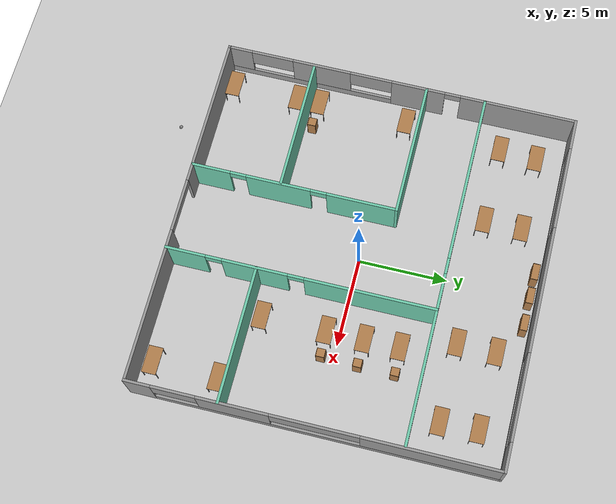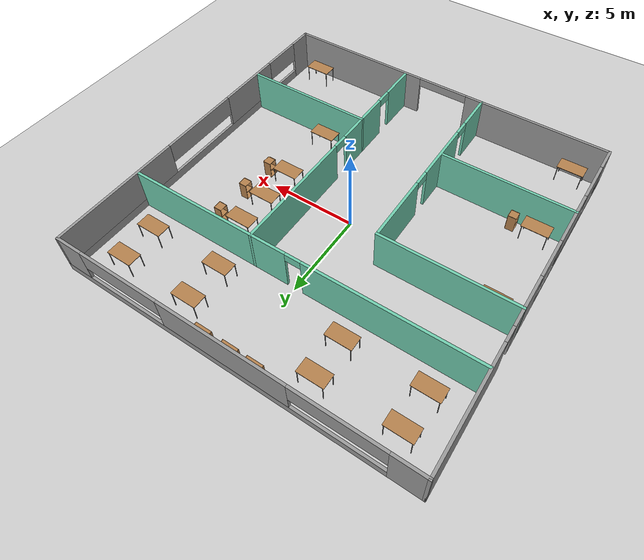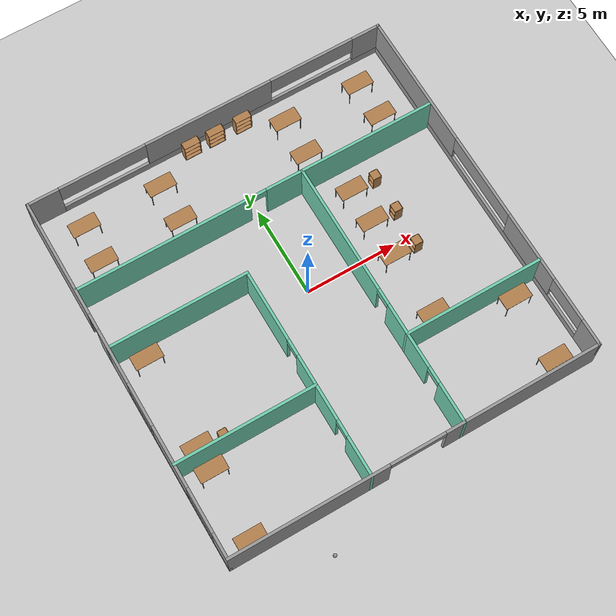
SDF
<sdf version="1.7">
 <world name="default">
  <light name="sun" type="directional">
   <pose>0 0 10 0 -0 0</pose>
   <diffuse>0.8 0.8 0.8 1</diffuse>
   <specular>0.2 0.2 0.2 1</specular>
   <attenuation>
    <range>1000</range>
    <constant>0.9</constant>
    <linear>0.01</linear>
    <quadratic>0.001</quadratic>
   </attenuation>
   <direction>-0.5 0.1 -0.9</direction>
   <spot><inner_angle>0</inner_angle><outer_angle>0</outer_angle><falloff>0</falloff></spot>
  </light>
  <model name="ground_plane">
   <static>1</static>
   <link name="link">
    <collision name="collision">
     <geometry><plane><normal>0 0 1</normal><size>100 100</size></plane></geometry>
     <surface>
      <contact><collide_bitmask>65535</collide_bitmask></contact>
      <friction><ode><mu>100</mu><mu2>50</mu2></ode></friction>
     </surface>
    </collision>
    <visual name="visual">
     <cast_shadows>0</cast_shadows>
     <geometry><plane><normal>0 0 1</normal><size>100 100</size></plane></geometry>
     <material>
      <script><uri>file://media/materials/scripts/gazebo.material</uri><name>Gazebo/Grey</name></script>
     </material>
    </visual>
   </link>
  </model>
  <gravity>0 0 -9.8</gravity>
  <magnetic_field>6e-06 2.3e-05 -4.2e-05</magnetic_field>
  <atmosphere type="adiabatic"/>
  <physics name="default_physics" default="0" type="ode">
   <max_step_size>0.001</max_step_size>
   <real_time_factor>1</real_time_factor>
   <real_time_update_rate>1000</real_time_update_rate>
  </physics>
  <scene><ambient>0.4 0.4 0.4 1</ambient><background>0.7 0.7 0.7 1</background><shadows>1</shadows></scene>
  <spherical_coordinates>
   <surface_model>EARTH_WGS84</surface_model>
   <latitude_deg>0</latitude_deg>
   <longitude_deg>0</longitude_deg>
   <elevation>0</elevation>
   <heading_deg>0</heading_deg>
  </spherical_coordinates>
  <model name="Building">
   <pose>0 -0.0025 0 0 -0 0</pose>
   <link name="Wall_0">
    <pose>0 10.0025 0 0 -0 0</pose>
    <visual name="Wall_0_Visual_0">
     <pose>-9.18922 0 1.25 0 -0 0</pose>
     <geometry><box><size>1.77156 0.15 2.5</size></box></geometry>
     <material>
      <script><uri>file://media/materials/scripts/gazebo.material</uri><name>Gazebo/Grey</name></script>
      <ambient>1 1 1 1</ambient>
     </material>
     <meta><layer>0</layer></meta>
    </visual>
    <collision name="Wall_0_Collision_0">
     <geometry><box><size>1.77156 0.15 2.5</size></box></geometry>
     <pose>-9.18922 0 1.25 0 -0 0</pose>
    </collision>
    <visual name="Wall_0_Visual_1">
     <pose>0.885782 0 0.25 0 -0 0</pose>
     <geometry><box><size>18.3784 0.15 0.5</size></box></geometry>
     <material>
      <script><uri>file://media/materials/scripts/gazebo.material</uri><name>Gazebo/Grey</name></script>
      <ambient>1 1 1 1</ambient>
     </material>
     <meta><layer>0</layer></meta>
    </visual>
    <collision name="Wall_0_Collision_1">
     <geometry><box><size>18.3784 0.15 0.5</size></box></geometry>
     <pose>0.885782 0 0.25 0 -0 0</pose>
    </collision>
    <visual name="Wall_0_Visual_2">
     <pose>0.068905 0 1.5 0 -0 0</pose>
     <geometry><box><size>7.14468 0.15 2</size></box></geometry>
     <material>
      <script><uri>file://media/materials/scripts/gazebo.material</uri><name>Gazebo/Grey</name></script>
      <ambient>1 1 1 1</ambient>
     </material>
     <meta><layer>0</layer></meta>
    </visual>
    <collision name="Wall_0_Collision_2">
     <geometry><box><size>7.14468 0.15 2</size></box></geometry>
     <pose>0.068905 0 1.5 0 -0 0</pose>
    </collision>
    <visual name="Wall_0_Visual_3">
     <pose>9.25812 0 1.5 0 -0 0</pose>
     <geometry><box><size>1.63375 0.15 2</size></box></geometry>
     <material>
      <script><uri>file://media/materials/scripts/gazebo.material</uri><name>Gazebo/Grey</name></script>
      <ambient>1 1 1 1</ambient>
     </material>
     <meta><layer>0</layer></meta>
    </visual>
    <collision name="Wall_0_Collision_3">
     <geometry><box><size>1.63375 0.15 2</size></box></geometry>
     <pose>9.25812 0 1.5 0 -0 0</pose>
    </collision>
    <visual name="Wall_0_Visual_4">
     <pose>-5.90344 0 1.9 0 -0 0</pose>
     <geometry><box><size>4.8 0.15 1.2</size></box></geometry>
     <material>
      <script><uri>file://media/materials/scripts/gazebo.material</uri><name>Gazebo/Grey</name></script>
      <ambient>1 1 1 1</ambient>
     </material>
     <meta><layer>0</layer></meta>
    </visual>
    <collision name="Wall_0_Collision_4">
     <geometry><box><size>4.8 0.15 1.2</size></box></geometry>
     <pose>-5.90344 0 1.9 0 -0 0</pose>
    </collision>
    <visual name="Wall_0_Visual_5">
     <pose>6.04125 0 1.9 0 -0 0</pose>
     <geometry><box><size>4.8 0.15 1.2</size></box></geometry>
     <material>
      <script><uri>file://media/materials/scripts/gazebo.material</uri><name>Gazebo/Grey</name></script>
      <ambient>1 1 1 1</ambient>
     </material>
     <meta><layer>0</layer></meta>
    </visual>
    <collision name="Wall_0_Collision_5">
     <geometry><box><size>4.8 0.15 1.2</size></box></geometry>
     <pose>6.04125 0 1.9 0 -0 0</pose>
    </collision>
   </link>
   <link name="Wall_10">
    <pose>-2.5 -4.3225 0 0 -0 1.5708</pose>
    <visual name="Wall_10_Visual_0">
     <pose>-4.63955 0 1.25 0 -0 0</pose>
     <geometry><box><size>2.2209 0.15 2.5</size></box></geometry>
     <material>
      <script><uri>file://media/materials/scripts/gazebo.material</uri><name>Gazebo/Grey</name></script>
      <ambient>0.435294 0.796078 0.67451 1</ambient>
     </material>
     <meta><layer>0</layer></meta>
    </visual>
    <collision name="Wall_10_Collision_0">
     <geometry><box><size>2.2209 0.15 2.5</size></box></geometry>
     <pose>-4.63955 0 1.25 0 -0 0</pose>
    </collision>
    <visual name="Wall_10_Visual_1">
     <pose>-0.81191 0 1.25 0 -0 0</pose>
     <geometry><box><size>3.63439 0.15 2.5</size></box></geometry>
     <material>
      <script><uri>file://media/materials/scripts/gazebo.material</uri><name>Gazebo/Grey</name></script>
      <ambient>0.435294 0.796078 0.67451 1</ambient>
     </material>
     <meta><layer>0</layer></meta>
    </visual>
    <collision name="Wall_10_Collision_1">
     <geometry><box><size>3.63439 0.15 2.5</size></box></geometry>
     <pose>-0.81191 0 1.25 0 -0 0</pose>
    </collision>
    <visual name="Wall_10_Visual_2">
     <pose>3.82764 0 1.25 0 -0 0</pose>
     <geometry><box><size>3.84472 0.15 2.5</size></box></geometry>
     <material>
      <script><uri>file://media/materials/scripts/gazebo.material</uri><name>Gazebo/Grey</name></script>
      <ambient>0.435294 0.796078 0.67451 1</ambient>
     </material>
     <meta><layer>0</layer></meta>
    </visual>
    <collision name="Wall_10_Collision_2">
     <geometry><box><size>3.84472 0.15 2.5</size></box></geometry>
     <pose>3.82764 0 1.25 0 -0 0</pose>
    </collision>
    <visual name="Wall_10_Visual_3">
     <pose>-3.0791 0 2.25 0 -0 0</pose>
     <geometry><box><size>0.9 0.15 0.5</size></box></geometry>
     <material>
      <script><uri>file://media/materials/scripts/gazebo.material</uri><name>Gazebo/Grey</name></script>
      <ambient>0.435294 0.796078 0.67451 1</ambient>
     </material>
     <meta><layer>0</layer></meta>
    </visual>
    <collision name="Wall_10_Collision_3">
     <geometry><box><size>0.9 0.15 0.5</size></box></geometry>
     <pose>-3.0791 0 2.25 0 -0 0</pose>
    </collision>
    <visual name="Wall_10_Visual_4">
     <pose>1.45528 0 2.25 0 -0 0</pose>
     <geometry><box><size>0.9 0.15 0.5</size></box></geometry>
     <material>
      <script><uri>file://media/materials/scripts/gazebo.material</uri><name>Gazebo/Grey</name></script>
      <ambient>0.435294 0.796078 0.67451 1</ambient>
     </material>
     <meta><layer>0</layer></meta>
    </visual>
    <collision name="Wall_10_Collision_4">
     <geometry><box><size>0.9 0.15 0.5</size></box></geometry>
     <pose>1.45528 0 2.25 0 -0 0</pose>
    </collision>
   </link>
   <link name="Wall_12">
    <pose>2.5 -2.5775 0 0 -0 1.5708</pose>
    <visual name="Wall_12_Visual_0">
     <pose>-6.37071 0 1.25 0 -0 0</pose>
     <geometry><box><size>2.25858 0.15 2.5</size></box></geometry>
     <material>
      <script><uri>file://media/materials/scripts/gazebo.material</uri><name>Gazebo/Grey</name></script>
      <ambient>0.435294 0.796078 0.67451 1</ambient>
     </material>
     <meta><layer>0</layer></meta>
    </visual>
    <collision name="Wall_12_Collision_0">
     <geometry><box><size>2.25858 0.15 2.5</size></box></geometry>
     <pose>-6.37071 0 1.25 0 -0 0</pose>
    </collision>
    <visual name="Wall_12_Visual_1">
     <pose>-2.52526 0 1.25 0 -0 0</pose>
     <geometry><box><size>3.63232 0.15 2.5</size></box></geometry>
     <material>
      <script><uri>file://media/materials/scripts/gazebo.material</uri><name>Gazebo/Grey</name></script>
      <ambient>0.435294 0.796078 0.67451 1</ambient>
     </material>
     <meta><layer>0</layer></meta>
    </visual>
    <collision name="Wall_12_Collision_1">
     <geometry><box><size>3.63232 0.15 2.5</size></box></geometry>
     <pose>-2.52526 0 1.25 0 -0 0</pose>
    </collision>
    <visual name="Wall_12_Visual_2">
     <pose>3.84545 0 1.25 0 -0 0</pose>
     <geometry><box><size>7.30909 0.15 2.5</size></box></geometry>
     <material>
      <script><uri>file://media/materials/scripts/gazebo.material</uri><name>Gazebo/Grey</name></script>
      <ambient>0.435294 0.796078 0.67451 1</ambient>
     </material>
     <meta><layer>0</layer></meta>
    </visual>
    <collision name="Wall_12_Collision_2">
     <geometry><box><size>7.30909 0.15 2.5</size></box></geometry>
     <pose>3.84545 0 1.25 0 -0 0</pose>
    </collision>
    <visual name="Wall_12_Visual_3">
     <pose>-4.79142 0 2.25 0 -0 0</pose>
     <geometry><box><size>0.9 0.15 0.5</size></box></geometry>
     <material>
      <script><uri>file://media/materials/scripts/gazebo.material</uri><name>Gazebo/Grey</name></script>
      <ambient>0.435294 0.796078 0.67451 1</ambient>
     </material>
     <meta><layer>0</layer></meta>
    </visual>
    <collision name="Wall_12_Collision_3">
     <geometry><box><size>0.9 0.15 0.5</size></box></geometry>
     <pose>-4.79142 0 2.25 0 -0 0</pose>
    </collision>
    <visual name="Wall_12_Visual_4">
     <pose>-0.259093 0 2.25 0 -0 0</pose>
     <geometry><box><size>0.9 0.15 0.5</size></box></geometry>
     <material>
      <script><uri>file://media/materials/scripts/gazebo.material</uri><name>Gazebo/Grey</name></script>
      <ambient>0.435294 0.796078 0.67451 1</ambient>
     </material>
     <meta><layer>0</layer></meta>
    </visual>
    <collision name="Wall_12_Collision_4">
     <geometry><box><size>0.9 0.15 0.5</size></box></geometry>
     <pose>-0.259093 0 2.25 0 -0 0</pose>
    </collision>
   </link>
   <link name="Wall_14">
    <collision name="Wall_14_Collision">
     <geometry><box><size>7.65 0.15 2.5</size></box></geometry>
     <pose>0 0 1.25 0 -0 0</pose>
    </collision>
    <visual name="Wall_14_Visual">
     <pose>0 0 1.25 0 -0 0</pose>
     <geometry><box><size>7.65 0.15 2.5</size></box></geometry>
     <material>
      <script><uri>file://media/materials/scripts/gazebo.material</uri><name>Gazebo/Grey</name></script>
      <ambient>0.435294 0.796078 0.67451 1</ambient>
     </material>
     <meta><layer>0</layer></meta>
    </visual>
    <pose>-6.25 1.5025 0 0 -0 0</pose>
   </link>
   <link name="Wall_16">
    <collision name="Wall_16_Collision">
     <geometry><box><size>7.65 0.15 2.5</size></box></geometry>
     <pose>0 0 1.25 0 -0 0</pose>
    </collision>
    <visual name="Wall_16_Visual">
     <pose>0 0 1.25 0 -0 0</pose>
     <geometry><box><size>7.65 0.15 2.5</size></box></geometry>
     <material>
      <script><uri>file://media/materials/scripts/gazebo.material</uri><name>Gazebo/Grey</name></script>
      <ambient>0.435294 0.796078 0.67451 1</ambient>
     </material>
     <meta><layer>0</layer></meta>
    </visual>
    <pose>-6.25 -4.9975 0 0 -0 0</pose>
   </link>
   <link name="Wall_18">
    <collision name="Wall_18_Collision">
     <geometry><box><size>7.65 0.15 2.5</size></box></geometry>
     <pose>0 0 1.25 0 -0 0</pose>
    </collision>
    <visual name="Wall_18_Visual">
     <pose>0 0 1.25 0 -0 0</pose>
     <geometry><box><size>7.65 0.15 2.5</size></box></geometry>
     <material>
      <script><uri>file://media/materials/scripts/gazebo.material</uri><name>Gazebo/Grey</name></script>
      <ambient>0.435294 0.796078 0.67451 1</ambient>
     </material>
     <meta><layer>0</layer></meta>
    </visual>
    <pose>6.25 -4.9975 0 0 -0 0</pose>
   </link>
   <link name="Wall_2">
    <pose>-10 0.0025 0 0 0 -1.5708</pose>
    <visual name="Wall_2_Visual_0">
     <pose>-6.7625 0 1.25 0 -0 0</pose>
     <geometry><box><size>6.625 0.15 2.5</size></box></geometry>
     <material>
      <script><uri>file://media/materials/scripts/gazebo.material</uri><name>Gazebo/Grey</name></script>
      <ambient>1 1 1 1</ambient>
     </material>
     <meta><layer>0</layer></meta>
    </visual>
    <collision name="Wall_2_Collision_0">
     <geometry><box><size>6.625 0.15 2.5</size></box></geometry>
     <pose>-6.7625 0 1.25 0 -0 0</pose>
    </collision>
    <visual name="Wall_2_Visual_1">
     <pose>-1.02199 0 1.25 0 -0 0</pose>
     <geometry><box><size>3.05601 0.15 2.5</size></box></geometry>
     <material>
      <script><uri>file://media/materials/scripts/gazebo.material</uri><name>Gazebo/Grey</name></script>
      <ambient>1 1 1 1</ambient>
     </material>
     <meta><layer>0</layer></meta>
    </visual>
    <collision name="Wall_2_Collision_1">
     <geometry><box><size>3.05601 0.15 2.5</size></box></geometry>
     <pose>-1.02199 0 1.25 0 -0 0</pose>
    </collision>
    <visual name="Wall_2_Visual_2">
     <pose>5.29051 0 0.25 0 -0 0</pose>
     <geometry><box><size>9.56899 0.15 0.5</size></box></geometry>
     <material>
      <script><uri>file://media/materials/scripts/gazebo.material</uri><name>Gazebo/Grey</name></script>
      <ambient>1 1 1 1</ambient>
     </material>
     <meta><layer>0</layer></meta>
    </visual>
    <collision name="Wall_2_Collision_2">
     <geometry><box><size>9.56899 0.15 0.5</size></box></geometry>
     <pose>5.29051 0 0.25 0 -0 0</pose>
    </collision>
    <visual name="Wall_2_Visual_3">
     <pose>4.58465 0 1.5 0 -0 0</pose>
     <geometry><box><size>3.35728 0.15 2</size></box></geometry>
     <material>
      <script><uri>file://media/materials/scripts/gazebo.material</uri><name>Gazebo/Grey</name></script>
      <ambient>1 1 1 1</ambient>
     </material>
     <meta><layer>0</layer></meta>
    </visual>
    <collision name="Wall_2_Collision_3">
     <geometry><box><size>3.35728 0.15 2</size></box></geometry>
     <pose>4.58465 0 1.5 0 -0 0</pose>
    </collision>
    <visual name="Wall_2_Visual_4">
     <pose>9.36914 0 1.5 0 -0 0</pose>
     <geometry><box><size>1.41171 0.15 2</size></box></geometry>
     <material>
      <script><uri>file://media/materials/scripts/gazebo.material</uri><name>Gazebo/Grey</name></script>
      <ambient>1 1 1 1</ambient>
     </material>
     <meta><layer>0</layer></meta>
    </visual>
    <collision name="Wall_2_Collision_4">
     <geometry><box><size>1.41171 0.15 2</size></box></geometry>
     <pose>9.36914 0 1.5 0 -0 0</pose>
    </collision>
    <visual name="Wall_2_Visual_5">
     <pose>1.70601 0 1.9 0 -0 0</pose>
     <geometry><box><size>2.4 0.15 1.2</size></box></geometry>
     <material>
      <script><uri>file://media/materials/scripts/gazebo.material</uri><name>Gazebo/Grey</name></script>
      <ambient>1 1 1 1</ambient>
     </material>
     <meta><layer>0</layer></meta>
    </visual>
    <collision name="Wall_2_Collision_5">
     <geometry><box><size>2.4 0.15 1.2</size></box></geometry>
     <pose>1.70601 0 1.9 0 -0 0</pose>
    </collision>
    <visual name="Wall_2_Visual_6">
     <pose>7.46329 0 1.9 0 -0 0</pose>
     <geometry><box><size>2.4 0.15 1.2</size></box></geometry>
     <material>
      <script><uri>file://media/materials/scripts/gazebo.material</uri><name>Gazebo/Grey</name></script>
      <ambient>1 1 1 1</ambient>
     </material>
     <meta><layer>0</layer></meta>
    </visual>
    <collision name="Wall_2_Collision_6">
     <geometry><box><size>2.4 0.15 1.2</size></box></geometry>
     <pose>7.46329 0 1.9 0 -0 0</pose>
    </collision>
    <visual name="Wall_2_Visual_7">
     <pose>-3 0 2.25 0 -0 0</pose>
     <geometry><box><size>0.9 0.15 0.5</size></box></geometry>
     <material>
      <script><uri>file://media/materials/scripts/gazebo.material</uri><name>Gazebo/Grey</name></script>
      <ambient>1 1 1 1</ambient>
     </material>
     <meta><layer>0</layer></meta>
    </visual>
    <collision name="Wall_2_Collision_7">
     <geometry><box><size>0.9 0.15 0.5</size></box></geometry>
     <pose>-3 0 2.25 0 -0 0</pose>
    </collision>
   </link>
   <link name="Wall_4">
    <pose>0 -9.9975 0 0 -0 0</pose>
    <visual name="Wall_4_Visual_0">
     <pose>-5.7875 0 1.25 0 -0 0</pose>
     <geometry><box><size>8.575 0.15 2.5</size></box></geometry>
     <material>
      <script><uri>file://media/materials/scripts/gazebo.material</uri><name>Gazebo/Grey</name></script>
      <ambient>1 1 1 1</ambient>
     </material>
     <meta><layer>0</layer></meta>
    </visual>
    <collision name="Wall_4_Collision_0">
     <geometry><box><size>8.575 0.15 2.5</size></box></geometry>
     <pose>-5.7875 0 1.25 0 -0 0</pose>
    </collision>
    <visual name="Wall_4_Visual_1">
     <pose>5.7875 0 1.25 0 -0 0</pose>
     <geometry><box><size>8.575 0.15 2.5</size></box></geometry>
     <material>
      <script><uri>file://media/materials/scripts/gazebo.material</uri><name>Gazebo/Grey</name></script>
      <ambient>1 1 1 1</ambient>
     </material>
     <meta><layer>0</layer></meta>
    </visual>
    <collision name="Wall_4_Collision_1">
     <geometry><box><size>8.575 0.15 2.5</size></box></geometry>
     <pose>5.7875 0 1.25 0 -0 0</pose>
    </collision>
    <visual name="Wall_4_Visual_2">
     <pose>0 0 2.25 0 -0 0</pose>
     <geometry><box><size>3 0.15 0.5</size></box></geometry>
     <material>
      <script><uri>file://media/materials/scripts/gazebo.material</uri><name>Gazebo/Grey</name></script>
      <ambient>1 1 1 1</ambient>
     </material>
     <meta><layer>0</layer></meta>
    </visual>
    <collision name="Wall_4_Collision_2">
     <geometry><box><size>3 0.15 0.5</size></box></geometry>
     <pose>0 0 2.25 0 -0 0</pose>
    </collision>
   </link>
   <link name="Wall_6">
    <pose>10 0.0025 0 0 -0 1.5708</pose>
    <visual name="Wall_6_Visual_0">
     <pose>-9.33852 0 1.25 0 -0 0</pose>
     <geometry><box><size>1.47296 0.15 2.5</size></box></geometry>
     <material>
      <script><uri>file://media/materials/scripts/gazebo.material</uri><name>Gazebo/Grey</name></script>
      <ambient>1 1 1 1</ambient>
     </material>
     <meta><layer>0</layer></meta>
    </visual>
    <collision name="Wall_6_Collision_0">
     <geometry><box><size>1.47296 0.15 2.5</size></box></geometry>
     <pose>-9.33852 0 1.25 0 -0 0</pose>
    </collision>
    <visual name="Wall_6_Visual_1">
     <pose>0.736479 0 0.25 0 -0 0</pose>
     <geometry><box><size>18.677 0.15 0.5</size></box></geometry>
     <material>
      <script><uri>file://media/materials/scripts/gazebo.material</uri><name>Gazebo/Grey</name></script>
      <ambient>1 1 1 1</ambient>
     </material>
     <meta><layer>0</layer></meta>
    </visual>
    <collision name="Wall_6_Collision_1">
     <geometry><box><size>18.677 0.15 0.5</size></box></geometry>
     <pose>0.736479 0 0.25 0 -0 0</pose>
    </collision>
    <visual name="Wall_6_Visual_2">
     <pose>-4.25062 0 1.5 0 -0 0</pose>
     <geometry><box><size>3.90284 0.15 2</size></box></geometry>
     <material>
      <script><uri>file://media/materials/scripts/gazebo.material</uri><name>Gazebo/Grey</name></script>
      <ambient>1 1 1 1</ambient>
     </material>
     <meta><layer>0</layer></meta>
    </visual>
    <collision name="Wall_6_Collision_2">
     <geometry><box><size>3.90284 0.15 2</size></box></geometry>
     <pose>-4.25062 0 1.5 0 -0 0</pose>
    </collision>
    <visual name="Wall_6_Visual_3">
     <pose>6.2879 0 1.5 0 -0 0</pose>
     <geometry><box><size>7.57421 0.15 2</size></box></geometry>
     <material>
      <script><uri>file://media/materials/scripts/gazebo.material</uri><name>Gazebo/Grey</name></script>
      <ambient>1 1 1 1</ambient>
     </material>
     <meta><layer>0</layer></meta>
    </visual>
    <collision name="Wall_6_Collision_3">
     <geometry><box><size>7.57421 0.15 2</size></box></geometry>
     <pose>6.2879 0 1.5 0 -0 0</pose>
    </collision>
    <visual name="Wall_6_Visual_4">
     <pose>-7.40204 0 1.9 0 -0 0</pose>
     <geometry><box><size>2.4 0.15 1.2</size></box></geometry>
     <material>
      <script><uri>file://media/materials/scripts/gazebo.material</uri><name>Gazebo/Grey</name></script>
      <ambient>1 1 1 1</ambient>
     </material>
     <meta><layer>0</layer></meta>
    </visual>
    <collision name="Wall_6_Collision_4">
     <geometry><box><size>2.4 0.15 1.2</size></box></geometry>
     <pose>-7.40204 0 1.9 0 -0 0</pose>
    </collision>
    <visual name="Wall_6_Visual_5">
     <pose>0.100793 0 1.9 0 -0 0</pose>
     <geometry><box><size>4.8 0.15 1.2</size></box></geometry>
     <material>
      <script><uri>file://media/materials/scripts/gazebo.material</uri><name>Gazebo/Grey</name></script>
      <ambient>1 1 1 1</ambient>
     </material>
     <meta><layer>0</layer></meta>
    </visual>
    <collision name="Wall_6_Collision_5">
     <geometry><box><size>4.8 0.15 1.2</size></box></geometry>
     <pose>0.100793 0 1.9 0 -0 0</pose>
    </collision>
   </link>
   <link name="Wall_8">
    <pose>-0.042815 4.84511 0 0 -0 0</pose>
    <visual name="Wall_8_Visual_0">
     <pose>-5.20359 0 1.25 0 -0 0</pose>
     <geometry><box><size>9.59281 0.15 2.5</size></box></geometry>
     <material>
      <script><uri>file://media/materials/scripts/gazebo.material</uri><name>Gazebo/Grey</name></script>
      <ambient>0.435294 0.796078 0.67451 1</ambient>
     </material>
     <meta><layer>0</layer></meta>
    </visual>
    <collision name="Wall_8_Collision_0">
     <geometry><box><size>9.59281 0.15 2.5</size></box></geometry>
     <pose>-5.20359 0 1.25 0 -0 0</pose>
    </collision>
    <visual name="Wall_8_Visual_1">
     <pose>5.24641 0 1.25 0 -0 0</pose>
     <geometry><box><size>9.50718 0.15 2.5</size></box></geometry>
     <material>
      <script><uri>file://media/materials/scripts/gazebo.material</uri><name>Gazebo/Grey</name></script>
      <ambient>0.435294 0.796078 0.67451 1</ambient>
     </material>
     <meta><layer>0</layer></meta>
    </visual>
    <collision name="Wall_8_Collision_1">
     <geometry><box><size>9.50718 0.15 2.5</size></box></geometry>
     <pose>5.24641 0 1.25 0 -0 0</pose>
    </collision>
    <visual name="Wall_8_Visual_2">
     <pose>0.042815 0 2.25 0 -0 0</pose>
     <geometry><box><size>0.9 0.15 0.5</size></box></geometry>
     <material>
      <script><uri>file://media/materials/scripts/gazebo.material</uri><name>Gazebo/Grey</name></script>
      <ambient>0.435294 0.796078 0.67451 1</ambient>
     </material>
     <meta><layer>0</layer></meta>
    </visual>
    <collision name="Wall_8_Collision_2">
     <geometry><box><size>0.9 0.15 0.5</size></box></geometry>
     <pose>0.042815 0 2.25 0 -0 0</pose>
    </collision>
   </link>
   <static>1</static>
  </model>
  <model name="table">
   <static>1</static>
   <link name="link">
    <collision name="surface">
     <pose>0 0 1 0 -0 0</pose>
     <geometry><box><size>1.5 0.8 0.03</size></box></geometry>
     <surface><friction><ode><mu>0.6</mu><mu2>0.6</mu2></ode></friction></surface>
    </collision>
    <visual name="visual1">
     <pose>0 0 1 0 -0 0</pose>
     <geometry><box><size>1.5 0.8 0.03</size></box></geometry>
     <material>
      <script><uri>file://media/materials/scripts/gazebo.material</uri><name>Gazebo/Wood</name></script>
     </material>
    </visual>
    <collision name="front_left_leg">
     <pose>0.68 0.38 0.5 0 -0 0</pose>
     <geometry><cylinder><radius>0.02</radius><length>1</length></cylinder></geometry>
    </collision>
    <visual name="front_left_leg">
     <pose>0.68 0.38 0.5 0 -0 0</pose>
     <geometry><cylinder><radius>0.02</radius><length>1</length></cylinder></geometry>
     <material>
      <script><uri>file://media/materials/scripts/gazebo.material</uri><name>Gazebo/Grey</name></script>
     </material>
    </visual>
    <collision name="front_right_leg">
     <pose>0.68 -0.38 0.5 0 -0 0</pose>
     <geometry><cylinder><radius>0.02</radius><length>1</length></cylinder></geometry>
    </collision>
    <visual name="front_right_leg">
     <pose>0.68 -0.38 0.5 0 -0 0</pose>
     <geometry><cylinder><radius>0.02</radius><length>1</length></cylinder></geometry>
     <material>
      <script><uri>file://media/materials/scripts/gazebo.material</uri><name>Gazebo/Grey</name></script>
     </material>
    </visual>
    <collision name="back_right_leg">
     <pose>-0.68 -0.38 0.5 0 -0 0</pose>
     <geometry><cylinder><radius>0.02</radius><length>1</length></cylinder></geometry>
    </collision>
    <visual name="back_right_leg">
     <pose>-0.68 -0.38 0.5 0 -0 0</pose>
     <geometry><cylinder><radius>0.02</radius><length>1</length></cylinder></geometry>
     <material>
      <script><uri>file://media/materials/scripts/gazebo.material</uri><name>Gazebo/Grey</name></script>
     </material>
    </visual>
    <collision name="back_left_leg">
     <pose>-0.68 0.38 0.5 0 -0 0</pose>
     <geometry><cylinder><radius>0.02</radius><length>1</length></cylinder></geometry>
    </collision>
    <visual name="back_left_leg">
     <pose>-0.68 0.38 0.5 0 -0 0</pose>
     <geometry><cylinder><radius>0.02</radius><length>1</length></cylinder></geometry>
     <material>
      <script><uri>file://media/materials/scripts/gazebo.material</uri><name>Gazebo/Grey</name></script>
     </material>
    </visual>
   </link>
   <pose>-8.53709 0.710616 0 0 -0 0</pose>
  </model>
  <model name="table_0">
   <static>1</static>
   <link name="link">
    <collision name="surface">
     <pose>0 0 1 0 -0 0</pose>
     <geometry><box><size>1.5 0.8 0.03</size></box></geometry>
     <surface><friction><ode><mu>0.6</mu><mu2>0.6</mu2></ode></friction></surface>
    </collision>
    <visual name="visual1">
     <pose>0 0 1 0 -0 0</pose>
     <geometry><box><size>1.5 0.8 0.03</size></box></geometry>
     <material>
      <script><uri>file://media/materials/scripts/gazebo.material</uri><name>Gazebo/Wood</name></script>
     </material>
    </visual>
    <collision name="front_left_leg">
     <pose>0.68 0.38 0.5 0 -0 0</pose>
     <geometry><cylinder><radius>0.02</radius><length>1</length></cylinder></geometry>
    </collision>
    <visual name="front_left_leg">
     <pose>0.68 0.38 0.5 0 -0 0</pose>
     <geometry><cylinder><radius>0.02</radius><length>1</length></cylinder></geometry>
     <material>
      <script><uri>file://media/materials/scripts/gazebo.material</uri><name>Gazebo/Grey</name></script>
     </material>
    </visual>
    <collision name="front_right_leg">
     <pose>0.68 -0.38 0.5 0 -0 0</pose>
     <geometry><cylinder><radius>0.02</radius><length>1</length></cylinder></geometry>
    </collision>
    <visual name="front_right_leg">
     <pose>0.68 -0.38 0.5 0 -0 0</pose>
     <geometry><cylinder><radius>0.02</radius><length>1</length></cylinder></geometry>
     <material>
      <script><uri>file://media/materials/scripts/gazebo.material</uri><name>Gazebo/Grey</name></script>
     </material>
    </visual>
    <collision name="back_right_leg">
     <pose>-0.68 -0.38 0.5 0 -0 0</pose>
     <geometry><cylinder><radius>0.02</radius><length>1</length></cylinder></geometry>
    </collision>
    <visual name="back_right_leg">
     <pose>-0.68 -0.38 0.5 0 -0 0</pose>
     <geometry><cylinder><radius>0.02</radius><length>1</length></cylinder></geometry>
     <material>
      <script><uri>file://media/materials/scripts/gazebo.material</uri><name>Gazebo/Grey</name></script>
     </material>
    </visual>
    <collision name="back_left_leg">
     <pose>-0.68 0.38 0.5 0 -0 0</pose>
     <geometry><cylinder><radius>0.02</radius><length>1</length></cylinder></geometry>
    </collision>
    <visual name="back_left_leg">
     <pose>-0.68 0.38 0.5 0 -0 0</pose>
     <geometry><cylinder><radius>0.02</radius><length>1</length></cylinder></geometry>
     <material>
      <script><uri>file://media/materials/scripts/gazebo.material</uri><name>Gazebo/Grey</name></script>
     </material>
    </visual>
   </link>
   <pose>-8.54272 -4.37684 0 0 -0 0</pose>
  </model>
  <model name="table_1">
   <static>1</static>
   <link name="link">
    <collision name="surface">
     <pose>0 0 1 0 -0 0</pose>
     <geometry><box><size>1.5 0.8 0.03</size></box></geometry>
     <surface><friction><ode><mu>0.6</mu><mu2>0.6</mu2></ode></friction></surface>
    </collision>
    <visual name="visual1">
     <pose>0 0 1 0 -0 0</pose>
     <geometry><box><size>1.5 0.8 0.03</size></box></geometry>
     <material>
      <script><uri>file://media/materials/scripts/gazebo.material</uri><name>Gazebo/Wood</name></script>
     </material>
    </visual>
    <collision name="front_left_leg">
     <pose>0.68 0.38 0.5 0 -0 0</pose>
     <geometry><cylinder><radius>0.02</radius><length>1</length></cylinder></geometry>
    </collision>
    <visual name="front_left_leg">
     <pose>0.68 0.38 0.5 0 -0 0</pose>
     <geometry><cylinder><radius>0.02</radius><length>1</length></cylinder></geometry>
     <material>
      <script><uri>file://media/materials/scripts/gazebo.material</uri><name>Gazebo/Grey</name></script>
     </material>
    </visual>
    <collision name="front_right_leg">
     <pose>0.68 -0.38 0.5 0 -0 0</pose>
     <geometry><cylinder><radius>0.02</radius><length>1</length></cylinder></geometry>
    </collision>
    <visual name="front_right_leg">
     <pose>0.68 -0.38 0.5 0 -0 0</pose>
     <geometry><cylinder><radius>0.02</radius><length>1</length></cylinder></geometry>
     <material>
      <script><uri>file://media/materials/scripts/gazebo.material</uri><name>Gazebo/Grey</name></script>
     </material>
    </visual>
    <collision name="back_right_leg">
     <pose>-0.68 -0.38 0.5 0 -0 0</pose>
     <geometry><cylinder><radius>0.02</radius><length>1</length></cylinder></geometry>
    </collision>
    <visual name="back_right_leg">
     <pose>-0.68 -0.38 0.5 0 -0 0</pose>
     <geometry><cylinder><radius>0.02</radius><length>1</length></cylinder></geometry>
     <material>
      <script><uri>file://media/materials/scripts/gazebo.material</uri><name>Gazebo/Grey</name></script>
     </material>
    </visual>
    <collision name="back_left_leg">
     <pose>-0.68 0.38 0.5 0 -0 0</pose>
     <geometry><cylinder><radius>0.02</radius><length>1</length></cylinder></geometry>
    </collision>
    <visual name="back_left_leg">
     <pose>-0.68 0.38 0.5 0 -0 0</pose>
     <geometry><cylinder><radius>0.02</radius><length>1</length></cylinder></geometry>
     <material>
      <script><uri>file://media/materials/scripts/gazebo.material</uri><name>Gazebo/Grey</name></script>
     </material>
    </visual>
   </link>
   <pose>-8.53135 -5.67134 0 0 -0 0</pose>
  </model>
  <model name="table_2">
   <static>1</static>
   <link name="link">
    <collision name="surface">
     <pose>0 0 1 0 -0 0</pose>
     <geometry><box><size>1.5 0.8 0.03</size></box></geometry>
     <surface><friction><ode><mu>0.6</mu><mu2>0.6</mu2></ode></friction></surface>
    </collision>
    <visual name="visual1">
     <pose>0 0 1 0 -0 0</pose>
     <geometry><box><size>1.5 0.8 0.03</size></box></geometry>
     <material>
      <script><uri>file://media/materials/scripts/gazebo.material</uri><name>Gazebo/Wood</name></script>
     </material>
    </visual>
    <collision name="front_left_leg">
     <pose>0.68 0.38 0.5 0 -0 0</pose>
     <geometry><cylinder><radius>0.02</radius><length>1</length></cylinder></geometry>
    </collision>
    <visual name="front_left_leg">
     <pose>0.68 0.38 0.5 0 -0 0</pose>
     <geometry><cylinder><radius>0.02</radius><length>1</length></cylinder></geometry>
     <material>
      <script><uri>file://media/materials/scripts/gazebo.material</uri><name>Gazebo/Grey</name></script>
     </material>
    </visual>
    <collision name="front_right_leg">
     <pose>0.68 -0.38 0.5 0 -0 0</pose>
     <geometry><cylinder><radius>0.02</radius><length>1</length></cylinder></geometry>
    </collision>
    <visual name="front_right_leg">
     <pose>0.68 -0.38 0.5 0 -0 0</pose>
     <geometry><cylinder><radius>0.02</radius><length>1</length></cylinder></geometry>
     <material>
      <script><uri>file://media/materials/scripts/gazebo.material</uri><name>Gazebo/Grey</name></script>
     </material>
    </visual>
    <collision name="back_right_leg">
     <pose>-0.68 -0.38 0.5 0 -0 0</pose>
     <geometry><cylinder><radius>0.02</radius><length>1</length></cylinder></geometry>
    </collision>
    <visual name="back_right_leg">
     <pose>-0.68 -0.38 0.5 0 -0 0</pose>
     <geometry><cylinder><radius>0.02</radius><length>1</length></cylinder></geometry>
     <material>
      <script><uri>file://media/materials/scripts/gazebo.material</uri><name>Gazebo/Grey</name></script>
     </material>
    </visual>
    <collision name="back_left_leg">
     <pose>-0.68 0.38 0.5 0 -0 0</pose>
     <geometry><cylinder><radius>0.02</radius><length>1</length></cylinder></geometry>
    </collision>
    <visual name="back_left_leg">
     <pose>-0.68 0.38 0.5 0 -0 0</pose>
     <geometry><cylinder><radius>0.02</radius><length>1</length></cylinder></geometry>
     <material>
      <script><uri>file://media/materials/scripts/gazebo.material</uri><name>Gazebo/Grey</name></script>
     </material>
    </visual>
   </link>
   <pose>-8.54251 -9.41407 0 0 -0 0</pose>
  </model>
  <model name="table_3">
   <static>1</static>
   <link name="link">
    <collision name="surface">
     <pose>0 0 1 0 -0 0</pose>
     <geometry><box><size>1.5 0.8 0.03</size></box></geometry>
     <surface><friction><ode><mu>0.6</mu><mu2>0.6</mu2></ode></friction></surface>
    </collision>
    <visual name="visual1">
     <pose>0 0 1 0 -0 0</pose>
     <geometry><box><size>1.5 0.8 0.03</size></box></geometry>
     <material>
      <script><uri>file://media/materials/scripts/gazebo.material</uri><name>Gazebo/Wood</name></script>
     </material>
    </visual>
    <collision name="front_left_leg">
     <pose>0.68 0.38 0.5 0 -0 0</pose>
     <geometry><cylinder><radius>0.02</radius><length>1</length></cylinder></geometry>
    </collision>
    <visual name="front_left_leg">
     <pose>0.68 0.38 0.5 0 -0 0</pose>
     <geometry><cylinder><radius>0.02</radius><length>1</length></cylinder></geometry>
     <material>
      <script><uri>file://media/materials/scripts/gazebo.material</uri><name>Gazebo/Grey</name></script>
     </material>
    </visual>
    <collision name="front_right_leg">
     <pose>0.68 -0.38 0.5 0 -0 0</pose>
     <geometry><cylinder><radius>0.02</radius><length>1</length></cylinder></geometry>
    </collision>
    <visual name="front_right_leg">
     <pose>0.68 -0.38 0.5 0 -0 0</pose>
     <geometry><cylinder><radius>0.02</radius><length>1</length></cylinder></geometry>
     <material>
      <script><uri>file://media/materials/scripts/gazebo.material</uri><name>Gazebo/Grey</name></script>
     </material>
    </visual>
    <collision name="back_right_leg">
     <pose>-0.68 -0.38 0.5 0 -0 0</pose>
     <geometry><cylinder><radius>0.02</radius><length>1</length></cylinder></geometry>
    </collision>
    <visual name="back_right_leg">
     <pose>-0.68 -0.38 0.5 0 -0 0</pose>
     <geometry><cylinder><radius>0.02</radius><length>1</length></cylinder></geometry>
     <material>
      <script><uri>file://media/materials/scripts/gazebo.material</uri><name>Gazebo/Grey</name></script>
     </material>
    </visual>
    <collision name="back_left_leg">
     <pose>-0.68 0.38 0.5 0 -0 0</pose>
     <geometry><cylinder><radius>0.02</radius><length>1</length></cylinder></geometry>
    </collision>
    <visual name="back_left_leg">
     <pose>-0.68 0.38 0.5 0 -0 0</pose>
     <geometry><cylinder><radius>0.02</radius><length>1</length></cylinder></geometry>
     <material>
      <script><uri>file://media/materials/scripts/gazebo.material</uri><name>Gazebo/Grey</name></script>
     </material>
    </visual>
   </link>
   <pose>8.39727 -5.61519 0 0 -0 0</pose>
  </model>
  <model name="table_4">
   <static>1</static>
   <link name="link">
    <collision name="surface">
     <pose>0 0 1 0 -0 0</pose>
     <geometry><box><size>1.5 0.8 0.03</size></box></geometry>
     <surface><friction><ode><mu>0.6</mu><mu2>0.6</mu2></ode></friction></surface>
    </collision>
    <visual name="visual1">
     <pose>0 0 1 0 -0 0</pose>
     <geometry><box><size>1.5 0.8 0.03</size></box></geometry>
     <material>
      <script><uri>file://media/materials/scripts/gazebo.material</uri><name>Gazebo/Wood</name></script>
     </material>
    </visual>
    <collision name="front_left_leg">
     <pose>0.68 0.38 0.5 0 -0 0</pose>
     <geometry><cylinder><radius>0.02</radius><length>1</length></cylinder></geometry>
    </collision>
    <visual name="front_left_leg">
     <pose>0.68 0.38 0.5 0 -0 0</pose>
     <geometry><cylinder><radius>0.02</radius><length>1</length></cylinder></geometry>
     <material>
      <script><uri>file://media/materials/scripts/gazebo.material</uri><name>Gazebo/Grey</name></script>
     </material>
    </visual>
    <collision name="front_right_leg">
     <pose>0.68 -0.38 0.5 0 -0 0</pose>
     <geometry><cylinder><radius>0.02</radius><length>1</length></cylinder></geometry>
    </collision>
    <visual name="front_right_leg">
     <pose>0.68 -0.38 0.5 0 -0 0</pose>
     <geometry><cylinder><radius>0.02</radius><length>1</length></cylinder></geometry>
     <material>
      <script><uri>file://media/materials/scripts/gazebo.material</uri><name>Gazebo/Grey</name></script>
     </material>
    </visual>
    <collision name="back_right_leg">
     <pose>-0.68 -0.38 0.5 0 -0 0</pose>
     <geometry><cylinder><radius>0.02</radius><length>1</length></cylinder></geometry>
    </collision>
    <visual name="back_right_leg">
     <pose>-0.68 -0.38 0.5 0 -0 0</pose>
     <geometry><cylinder><radius>0.02</radius><length>1</length></cylinder></geometry>
     <material>
      <script><uri>file://media/materials/scripts/gazebo.material</uri><name>Gazebo/Grey</name></script>
     </material>
    </visual>
    <collision name="back_left_leg">
     <pose>-0.68 0.38 0.5 0 -0 0</pose>
     <geometry><cylinder><radius>0.02</radius><length>1</length></cylinder></geometry>
    </collision>
    <visual name="back_left_leg">
     <pose>-0.68 0.38 0.5 0 -0 0</pose>
     <geometry><cylinder><radius>0.02</radius><length>1</length></cylinder></geometry>
     <material>
      <script><uri>file://media/materials/scripts/gazebo.material</uri><name>Gazebo/Grey</name></script>
     </material>
    </visual>
   </link>
   <pose>8.32406 -9.22945 0 0 -0 0</pose>
  </model>
  <model name="table_5">
   <static>1</static>
   <link name="link">
    <collision name="surface">
     <pose>0 0 1 0 -0 0</pose>
     <geometry><box><size>1.5 0.8 0.03</size></box></geometry>
     <surface><friction><ode><mu>0.6</mu><mu2>0.6</mu2></ode></friction></surface>
    </collision>
    <visual name="visual1">
     <pose>0 0 1 0 -0 0</pose>
     <geometry><box><size>1.5 0.8 0.03</size></box></geometry>
     <material>
      <script><uri>file://media/materials/scripts/gazebo.material</uri><name>Gazebo/Wood</name></script>
     </material>
    </visual>
    <collision name="front_left_leg">
     <pose>0.68 0.38 0.5 0 -0 0</pose>
     <geometry><cylinder><radius>0.02</radius><length>1</length></cylinder></geometry>
    </collision>
    <visual name="front_left_leg">
     <pose>0.68 0.38 0.5 0 -0 0</pose>
     <geometry><cylinder><radius>0.02</radius><length>1</length></cylinder></geometry>
     <material>
      <script><uri>file://media/materials/scripts/gazebo.material</uri><name>Gazebo/Grey</name></script>
     </material>
    </visual>
    <collision name="front_right_leg">
     <pose>0.68 -0.38 0.5 0 -0 0</pose>
     <geometry><cylinder><radius>0.02</radius><length>1</length></cylinder></geometry>
    </collision>
    <visual name="front_right_leg">
     <pose>0.68 -0.38 0.5 0 -0 0</pose>
     <geometry><cylinder><radius>0.02</radius><length>1</length></cylinder></geometry>
     <material>
      <script><uri>file://media/materials/scripts/gazebo.material</uri><name>Gazebo/Grey</name></script>
     </material>
    </visual>
    <collision name="back_right_leg">
     <pose>-0.68 -0.38 0.5 0 -0 0</pose>
     <geometry><cylinder><radius>0.02</radius><length>1</length></cylinder></geometry>
    </collision>
    <visual name="back_right_leg">
     <pose>-0.68 -0.38 0.5 0 -0 0</pose>
     <geometry><cylinder><radius>0.02</radius><length>1</length></cylinder></geometry>
     <material>
      <script><uri>file://media/materials/scripts/gazebo.material</uri><name>Gazebo/Grey</name></script>
     </material>
    </visual>
    <collision name="back_left_leg">
     <pose>-0.68 0.38 0.5 0 -0 0</pose>
     <geometry><cylinder><radius>0.02</radius><length>1</length></cylinder></geometry>
    </collision>
    <visual name="back_left_leg">
     <pose>-0.68 0.38 0.5 0 -0 0</pose>
     <geometry><cylinder><radius>0.02</radius><length>1</length></cylinder></geometry>
     <material>
      <script><uri>file://media/materials/scripts/gazebo.material</uri><name>Gazebo/Grey</name></script>
     </material>
    </visual>
   </link>
   <pose>4.50079 3.36839 0 0 -0 0</pose>
  </model>
  <model name="table_6">
   <static>1</static>
   <link name="link">
    <collision name="surface">
     <pose>0 0 1 0 -0 0</pose>
     <geometry><box><size>1.5 0.8 0.03</size></box></geometry>
     <surface><friction><ode><mu>0.6</mu><mu2>0.6</mu2></ode></friction></surface>
    </collision>
    <visual name="visual1">
     <pose>0 0 1 0 -0 0</pose>
     <geometry><box><size>1.5 0.8 0.03</size></box></geometry>
     <material>
      <script><uri>file://media/materials/scripts/gazebo.material</uri><name>Gazebo/Wood</name></script>
     </material>
    </visual>
    <collision name="front_left_leg">
     <pose>0.68 0.38 0.5 0 -0 0</pose>
     <geometry><cylinder><radius>0.02</radius><length>1</length></cylinder></geometry>
    </collision>
    <visual name="front_left_leg">
     <pose>0.68 0.38 0.5 0 -0 0</pose>
     <geometry><cylinder><radius>0.02</radius><length>1</length></cylinder></geometry>
     <material>
      <script><uri>file://media/materials/scripts/gazebo.material</uri><name>Gazebo/Grey</name></script>
     </material>
    </visual>
    <collision name="front_right_leg">
     <pose>0.68 -0.38 0.5 0 -0 0</pose>
     <geometry><cylinder><radius>0.02</radius><length>1</length></cylinder></geometry>
    </collision>
    <visual name="front_right_leg">
     <pose>0.68 -0.38 0.5 0 -0 0</pose>
     <geometry><cylinder><radius>0.02</radius><length>1</length></cylinder></geometry>
     <material>
      <script><uri>file://media/materials/scripts/gazebo.material</uri><name>Gazebo/Grey</name></script>
     </material>
    </visual>
    <collision name="back_right_leg">
     <pose>-0.68 -0.38 0.5 0 -0 0</pose>
     <geometry><cylinder><radius>0.02</radius><length>1</length></cylinder></geometry>
    </collision>
    <visual name="back_right_leg">
     <pose>-0.68 -0.38 0.5 0 -0 0</pose>
     <geometry><cylinder><radius>0.02</radius><length>1</length></cylinder></geometry>
     <material>
      <script><uri>file://media/materials/scripts/gazebo.material</uri><name>Gazebo/Grey</name></script>
     </material>
    </visual>
    <collision name="back_left_leg">
     <pose>-0.68 0.38 0.5 0 -0 0</pose>
     <geometry><cylinder><radius>0.02</radius><length>1</length></cylinder></geometry>
    </collision>
    <visual name="back_left_leg">
     <pose>-0.68 0.38 0.5 0 -0 0</pose>
     <geometry><cylinder><radius>0.02</radius><length>1</length></cylinder></geometry>
     <material>
      <script><uri>file://media/materials/scripts/gazebo.material</uri><name>Gazebo/Grey</name></script>
     </material>
    </visual>
   </link>
   <pose>4.52318 1.40941 0 0 -0 0</pose>
  </model>
  <model name="table_7">
   <static>1</static>
   <link name="link">
    <collision name="surface">
     <pose>0 0 1 0 -0 0</pose>
     <geometry><box><size>1.5 0.8 0.03</size></box></geometry>
     <surface><friction><ode><mu>0.6</mu><mu2>0.6</mu2></ode></friction></surface>
    </collision>
    <visual name="visual1">
     <pose>0 0 1 0 -0 0</pose>
     <geometry><box><size>1.5 0.8 0.03</size></box></geometry>
     <material>
      <script><uri>file://media/materials/scripts/gazebo.material</uri><name>Gazebo/Wood</name></script>
     </material>
    </visual>
    <collision name="front_left_leg">
     <pose>0.68 0.38 0.5 0 -0 0</pose>
     <geometry><cylinder><radius>0.02</radius><length>1</length></cylinder></geometry>
    </collision>
    <visual name="front_left_leg">
     <pose>0.68 0.38 0.5 0 -0 0</pose>
     <geometry><cylinder><radius>0.02</radius><length>1</length></cylinder></geometry>
     <material>
      <script><uri>file://media/materials/scripts/gazebo.material</uri><name>Gazebo/Grey</name></script>
     </material>
    </visual>
    <collision name="front_right_leg">
     <pose>0.68 -0.38 0.5 0 -0 0</pose>
     <geometry><cylinder><radius>0.02</radius><length>1</length></cylinder></geometry>
    </collision>
    <visual name="front_right_leg">
     <pose>0.68 -0.38 0.5 0 -0 0</pose>
     <geometry><cylinder><radius>0.02</radius><length>1</length></cylinder></geometry>
     <material>
      <script><uri>file://media/materials/scripts/gazebo.material</uri><name>Gazebo/Grey</name></script>
     </material>
    </visual>
    <collision name="back_right_leg">
     <pose>-0.68 -0.38 0.5 0 -0 0</pose>
     <geometry><cylinder><radius>0.02</radius><length>1</length></cylinder></geometry>
    </collision>
    <visual name="back_right_leg">
     <pose>-0.68 -0.38 0.5 0 -0 0</pose>
     <geometry><cylinder><radius>0.02</radius><length>1</length></cylinder></geometry>
     <material>
      <script><uri>file://media/materials/scripts/gazebo.material</uri><name>Gazebo/Grey</name></script>
     </material>
    </visual>
    <collision name="back_left_leg">
     <pose>-0.68 0.38 0.5 0 -0 0</pose>
     <geometry><cylinder><radius>0.02</radius><length>1</length></cylinder></geometry>
    </collision>
    <visual name="back_left_leg">
     <pose>-0.68 0.38 0.5 0 -0 0</pose>
     <geometry><cylinder><radius>0.02</radius><length>1</length></cylinder></geometry>
     <material>
      <script><uri>file://media/materials/scripts/gazebo.material</uri><name>Gazebo/Grey</name></script>
     </material>
    </visual>
   </link>
   <pose>4.5428 -0.688026 0 0 -0 0</pose>
  </model>
  <model name="table_8">
   <static>1</static>
   <link name="link">
    <collision name="surface">
     <pose>0 0 1 0 -0 0</pose>
     <geometry><box><size>1.5 0.8 0.03</size></box></geometry>
     <surface><friction><ode><mu>0.6</mu><mu2>0.6</mu2></ode></friction></surface>
    </collision>
    <visual name="visual1">
     <pose>0 0 1 0 -0 0</pose>
     <geometry><box><size>1.5 0.8 0.03</size></box></geometry>
     <material>
      <script><uri>file://media/materials/scripts/gazebo.material</uri><name>Gazebo/Wood</name></script>
     </material>
    </visual>
    <collision name="front_left_leg">
     <pose>0.68 0.38 0.5 0 -0 0</pose>
     <geometry><cylinder><radius>0.02</radius><length>1</length></cylinder></geometry>
    </collision>
    <visual name="front_left_leg">
     <pose>0.68 0.38 0.5 0 -0 0</pose>
     <geometry><cylinder><radius>0.02</radius><length>1</length></cylinder></geometry>
     <material>
      <script><uri>file://media/materials/scripts/gazebo.material</uri><name>Gazebo/Grey</name></script>
     </material>
    </visual>
    <collision name="front_right_leg">
     <pose>0.68 -0.38 0.5 0 -0 0</pose>
     <geometry><cylinder><radius>0.02</radius><length>1</length></cylinder></geometry>
    </collision>
    <visual name="front_right_leg">
     <pose>0.68 -0.38 0.5 0 -0 0</pose>
     <geometry><cylinder><radius>0.02</radius><length>1</length></cylinder></geometry>
     <material>
      <script><uri>file://media/materials/scripts/gazebo.material</uri><name>Gazebo/Grey</name></script>
     </material>
    </visual>
    <collision name="back_right_leg">
     <pose>-0.68 -0.38 0.5 0 -0 0</pose>
     <geometry><cylinder><radius>0.02</radius><length>1</length></cylinder></geometry>
    </collision>
    <visual name="back_right_leg">
     <pose>-0.68 -0.38 0.5 0 -0 0</pose>
     <geometry><cylinder><radius>0.02</radius><length>1</length></cylinder></geometry>
     <material>
      <script><uri>file://media/materials/scripts/gazebo.material</uri><name>Gazebo/Grey</name></script>
     </material>
    </visual>
    <collision name="back_left_leg">
     <pose>-0.68 0.38 0.5 0 -0 0</pose>
     <geometry><cylinder><radius>0.02</radius><length>1</length></cylinder></geometry>
    </collision>
    <visual name="back_left_leg">
     <pose>-0.68 0.38 0.5 0 -0 0</pose>
     <geometry><cylinder><radius>0.02</radius><length>1</length></cylinder></geometry>
     <material>
      <script><uri>file://media/materials/scripts/gazebo.material</uri><name>Gazebo/Grey</name></script>
     </material>
    </visual>
   </link>
   <pose>4.55416 -4.27473 0 0 -0 0</pose>
  </model>
  <model name="table_9">
   <static>1</static>
   <link name="link">
    <collision name="surface">
     <pose>0 0 1 0 -0 0</pose>
     <geometry><box><size>1.5 0.8 0.03</size></box></geometry>
     <surface><friction><ode><mu>0.6</mu><mu2>0.6</mu2></ode></friction></surface>
    </collision>
    <visual name="visual1">
     <pose>0 0 1 0 -0 0</pose>
     <geometry><box><size>1.5 0.8 0.03</size></box></geometry>
     <material>
      <script><uri>file://media/materials/scripts/gazebo.material</uri><name>Gazebo/Wood</name></script>
     </material>
    </visual>
    <collision name="front_left_leg">
     <pose>0.68 0.38 0.5 0 -0 0</pose>
     <geometry><cylinder><radius>0.02</radius><length>1</length></cylinder></geometry>
    </collision>
    <visual name="front_left_leg">
     <pose>0.68 0.38 0.5 0 -0 0</pose>
     <geometry><cylinder><radius>0.02</radius><length>1</length></cylinder></geometry>
     <material>
      <script><uri>file://media/materials/scripts/gazebo.material</uri><name>Gazebo/Grey</name></script>
     </material>
    </visual>
    <collision name="front_right_leg">
     <pose>0.68 -0.38 0.5 0 -0 0</pose>
     <geometry><cylinder><radius>0.02</radius><length>1</length></cylinder></geometry>
    </collision>
    <visual name="front_right_leg">
     <pose>0.68 -0.38 0.5 0 -0 0</pose>
     <geometry><cylinder><radius>0.02</radius><length>1</length></cylinder></geometry>
     <material>
      <script><uri>file://media/materials/scripts/gazebo.material</uri><name>Gazebo/Grey</name></script>
     </material>
    </visual>
    <collision name="back_right_leg">
     <pose>-0.68 -0.38 0.5 0 -0 0</pose>
     <geometry><cylinder><radius>0.02</radius><length>1</length></cylinder></geometry>
    </collision>
    <visual name="back_right_leg">
     <pose>-0.68 -0.38 0.5 0 -0 0</pose>
     <geometry><cylinder><radius>0.02</radius><length>1</length></cylinder></geometry>
     <material>
      <script><uri>file://media/materials/scripts/gazebo.material</uri><name>Gazebo/Grey</name></script>
     </material>
    </visual>
    <collision name="back_left_leg">
     <pose>-0.68 0.38 0.5 0 -0 0</pose>
     <geometry><cylinder><radius>0.02</radius><length>1</length></cylinder></geometry>
    </collision>
    <visual name="back_left_leg">
     <pose>-0.68 0.38 0.5 0 -0 0</pose>
     <geometry><cylinder><radius>0.02</radius><length>1</length></cylinder></geometry>
     <material>
      <script><uri>file://media/materials/scripts/gazebo.material</uri><name>Gazebo/Grey</name></script>
     </material>
    </visual>
   </link>
   <pose>-7.98606 8.34113 0 0 -0 0</pose>
  </model>
  <model name="table_10">
   <static>1</static>
   <link name="link">
    <collision name="surface">
     <pose>0 0 1 0 -0 0</pose>
     <geometry><box><size>1.5 0.8 0.03</size></box></geometry>
     <surface><friction><ode><mu>0.6</mu><mu2>0.6</mu2></ode></friction></surface>
    </collision>
    <visual name="visual1">
     <pose>0 0 1 0 -0 0</pose>
     <geometry><box><size>1.5 0.8 0.03</size></box></geometry>
     <material>
      <script><uri>file://media/materials/scripts/gazebo.material</uri><name>Gazebo/Wood</name></script>
     </material>
    </visual>
    <collision name="front_left_leg">
     <pose>0.68 0.38 0.5 0 -0 0</pose>
     <geometry><cylinder><radius>0.02</radius><length>1</length></cylinder></geometry>
    </collision>
    <visual name="front_left_leg">
     <pose>0.68 0.38 0.5 0 -0 0</pose>
     <geometry><cylinder><radius>0.02</radius><length>1</length></cylinder></geometry>
     <material>
      <script><uri>file://media/materials/scripts/gazebo.material</uri><name>Gazebo/Grey</name></script>
     </material>
    </visual>
    <collision name="front_right_leg">
     <pose>0.68 -0.38 0.5 0 -0 0</pose>
     <geometry><cylinder><radius>0.02</radius><length>1</length></cylinder></geometry>
    </collision>
    <visual name="front_right_leg">
     <pose>0.68 -0.38 0.5 0 -0 0</pose>
     <geometry><cylinder><radius>0.02</radius><length>1</length></cylinder></geometry>
     <material>
      <script><uri>file://media/materials/scripts/gazebo.material</uri><name>Gazebo/Grey</name></script>
     </material>
    </visual>
    <collision name="back_right_leg">
     <pose>-0.68 -0.38 0.5 0 -0 0</pose>
     <geometry><cylinder><radius>0.02</radius><length>1</length></cylinder></geometry>
    </collision>
    <visual name="back_right_leg">
     <pose>-0.68 -0.38 0.5 0 -0 0</pose>
     <geometry><cylinder><radius>0.02</radius><length>1</length></cylinder></geometry>
     <material>
      <script><uri>file://media/materials/scripts/gazebo.material</uri><name>Gazebo/Grey</name></script>
     </material>
    </visual>
    <collision name="back_left_leg">
     <pose>-0.68 0.38 0.5 0 -0 0</pose>
     <geometry><cylinder><radius>0.02</radius><length>1</length></cylinder></geometry>
    </collision>
    <visual name="back_left_leg">
     <pose>-0.68 0.38 0.5 0 -0 0</pose>
     <geometry><cylinder><radius>0.02</radius><length>1</length></cylinder></geometry>
     <material>
      <script><uri>file://media/materials/scripts/gazebo.material</uri><name>Gazebo/Grey</name></script>
     </material>
    </visual>
   </link>
   <pose>-3.67482 8.39003 0 0 -0 0</pose>
  </model>
  <model name="table_11">
   <static>1</static>
   <link name="link">
    <collision name="surface">
     <pose>0 0 1 0 -0 0</pose>
     <geometry><box><size>1.5 0.8 0.03</size></box></geometry>
     <surface><friction><ode><mu>0.6</mu><mu2>0.6</mu2></ode></friction></surface>
    </collision>
    <visual name="visual1">
     <pose>0 0 1 0 -0 0</pose>
     <geometry><box><size>1.5 0.8 0.03</size></box></geometry>
     <material>
      <script><uri>file://media/materials/scripts/gazebo.material</uri><name>Gazebo/Wood</name></script>
     </material>
    </visual>
    <collision name="front_left_leg">
     <pose>0.68 0.38 0.5 0 -0 0</pose>
     <geometry><cylinder><radius>0.02</radius><length>1</length></cylinder></geometry>
    </collision>
    <visual name="front_left_leg">
     <pose>0.68 0.38 0.5 0 -0 0</pose>
     <geometry><cylinder><radius>0.02</radius><length>1</length></cylinder></geometry>
     <material>
      <script><uri>file://media/materials/scripts/gazebo.material</uri><name>Gazebo/Grey</name></script>
     </material>
    </visual>
    <collision name="front_right_leg">
     <pose>0.68 -0.38 0.5 0 -0 0</pose>
     <geometry><cylinder><radius>0.02</radius><length>1</length></cylinder></geometry>
    </collision>
    <visual name="front_right_leg">
     <pose>0.68 -0.38 0.5 0 -0 0</pose>
     <geometry><cylinder><radius>0.02</radius><length>1</length></cylinder></geometry>
     <material>
      <script><uri>file://media/materials/scripts/gazebo.material</uri><name>Gazebo/Grey</name></script>
     </material>
    </visual>
    <collision name="back_right_leg">
     <pose>-0.68 -0.38 0.5 0 -0 0</pose>
     <geometry><cylinder><radius>0.02</radius><length>1</length></cylinder></geometry>
    </collision>
    <visual name="back_right_leg">
     <pose>-0.68 -0.38 0.5 0 -0 0</pose>
     <geometry><cylinder><radius>0.02</radius><length>1</length></cylinder></geometry>
     <material>
      <script><uri>file://media/materials/scripts/gazebo.material</uri><name>Gazebo/Grey</name></script>
     </material>
    </visual>
    <collision name="back_left_leg">
     <pose>-0.68 0.38 0.5 0 -0 0</pose>
     <geometry><cylinder><radius>0.02</radius><length>1</length></cylinder></geometry>
    </collision>
    <visual name="back_left_leg">
     <pose>-0.68 0.38 0.5 0 -0 0</pose>
     <geometry><cylinder><radius>0.02</radius><length>1</length></cylinder></geometry>
     <material>
      <script><uri>file://media/materials/scripts/gazebo.material</uri><name>Gazebo/Grey</name></script>
     </material>
    </visual>
   </link>
   <pose>-8.09236 6.25425 0 0 -0 0</pose>
  </model>
  <model name="table_12">
   <static>1</static>
   <link name="link">
    <collision name="surface">
     <pose>0 0 1 0 -0 0</pose>
     <geometry><box><size>1.5 0.8 0.03</size></box></geometry>
     <surface><friction><ode><mu>0.6</mu><mu2>0.6</mu2></ode></friction></surface>
    </collision>
    <visual name="visual1">
     <pose>0 0 1 0 -0 0</pose>
     <geometry><box><size>1.5 0.8 0.03</size></box></geometry>
     <material>
      <script><uri>file://media/materials/scripts/gazebo.material</uri><name>Gazebo/Wood</name></script>
     </material>
    </visual>
    <collision name="front_left_leg">
     <pose>0.68 0.38 0.5 0 -0 0</pose>
     <geometry><cylinder><radius>0.02</radius><length>1</length></cylinder></geometry>
    </collision>
    <visual name="front_left_leg">
     <pose>0.68 0.38 0.5 0 -0 0</pose>
     <geometry><cylinder><radius>0.02</radius><length>1</length></cylinder></geometry>
     <material>
      <script><uri>file://media/materials/scripts/gazebo.material</uri><name>Gazebo/Grey</name></script>
     </material>
    </visual>
    <collision name="front_right_leg">
     <pose>0.68 -0.38 0.5 0 -0 0</pose>
     <geometry><cylinder><radius>0.02</radius><length>1</length></cylinder></geometry>
    </collision>
    <visual name="front_right_leg">
     <pose>0.68 -0.38 0.5 0 -0 0</pose>
     <geometry><cylinder><radius>0.02</radius><length>1</length></cylinder></geometry>
     <material>
      <script><uri>file://media/materials/scripts/gazebo.material</uri><name>Gazebo/Grey</name></script>
     </material>
    </visual>
    <collision name="back_right_leg">
     <pose>-0.68 -0.38 0.5 0 -0 0</pose>
     <geometry><cylinder><radius>0.02</radius><length>1</length></cylinder></geometry>
    </collision>
    <visual name="back_right_leg">
     <pose>-0.68 -0.38 0.5 0 -0 0</pose>
     <geometry><cylinder><radius>0.02</radius><length>1</length></cylinder></geometry>
     <material>
      <script><uri>file://media/materials/scripts/gazebo.material</uri><name>Gazebo/Grey</name></script>
     </material>
    </visual>
    <collision name="back_left_leg">
     <pose>-0.68 0.38 0.5 0 -0 0</pose>
     <geometry><cylinder><radius>0.02</radius><length>1</length></cylinder></geometry>
    </collision>
    <visual name="back_left_leg">
     <pose>-0.68 0.38 0.5 0 -0 0</pose>
     <geometry><cylinder><radius>0.02</radius><length>1</length></cylinder></geometry>
     <material>
      <script><uri>file://media/materials/scripts/gazebo.material</uri><name>Gazebo/Grey</name></script>
     </material>
    </visual>
   </link>
   <pose>-3.68213 6.26365 0 0 -0 0</pose>
  </model>
  <model name="table_13">
   <static>1</static>
   <link name="link">
    <collision name="surface">
     <pose>0 0 1 0 -0 0</pose>
     <geometry><box><size>1.5 0.8 0.03</size></box></geometry>
     <surface><friction><ode><mu>0.6</mu><mu2>0.6</mu2></ode></friction></surface>
    </collision>
    <visual name="visual1">
     <pose>0 0 1 0 -0 0</pose>
     <geometry><box><size>1.5 0.8 0.03</size></box></geometry>
     <material>
      <script><uri>file://media/materials/scripts/gazebo.material</uri><name>Gazebo/Wood</name></script>
     </material>
    </visual>
    <collision name="front_left_leg">
     <pose>0.68 0.38 0.5 0 -0 0</pose>
     <geometry><cylinder><radius>0.02</radius><length>1</length></cylinder></geometry>
    </collision>
    <visual name="front_left_leg">
     <pose>0.68 0.38 0.5 0 -0 0</pose>
     <geometry><cylinder><radius>0.02</radius><length>1</length></cylinder></geometry>
     <material>
      <script><uri>file://media/materials/scripts/gazebo.material</uri><name>Gazebo/Grey</name></script>
     </material>
    </visual>
    <collision name="front_right_leg">
     <pose>0.68 -0.38 0.5 0 -0 0</pose>
     <geometry><cylinder><radius>0.02</radius><length>1</length></cylinder></geometry>
    </collision>
    <visual name="front_right_leg">
     <pose>0.68 -0.38 0.5 0 -0 0</pose>
     <geometry><cylinder><radius>0.02</radius><length>1</length></cylinder></geometry>
     <material>
      <script><uri>file://media/materials/scripts/gazebo.material</uri><name>Gazebo/Grey</name></script>
     </material>
    </visual>
    <collision name="back_right_leg">
     <pose>-0.68 -0.38 0.5 0 -0 0</pose>
     <geometry><cylinder><radius>0.02</radius><length>1</length></cylinder></geometry>
    </collision>
    <visual name="back_right_leg">
     <pose>-0.68 -0.38 0.5 0 -0 0</pose>
     <geometry><cylinder><radius>0.02</radius><length>1</length></cylinder></geometry>
     <material>
      <script><uri>file://media/materials/scripts/gazebo.material</uri><name>Gazebo/Grey</name></script>
     </material>
    </visual>
    <collision name="back_left_leg">
     <pose>-0.68 0.38 0.5 0 -0 0</pose>
     <geometry><cylinder><radius>0.02</radius><length>1</length></cylinder></geometry>
    </collision>
    <visual name="back_left_leg">
     <pose>-0.68 0.38 0.5 0 -0 0</pose>
     <geometry><cylinder><radius>0.02</radius><length>1</length></cylinder></geometry>
     <material>
      <script><uri>file://media/materials/scripts/gazebo.material</uri><name>Gazebo/Grey</name></script>
     </material>
    </visual>
   </link>
   <pose>3.57065 8.41018 0 0 -0 0</pose>
  </model>
  <model name="table_14">
   <static>1</static>
   <link name="link">
    <collision name="surface">
     <pose>0 0 1 0 -0 0</pose>
     <geometry><box><size>1.5 0.8 0.03</size></box></geometry>
     <surface><friction><ode><mu>0.6</mu><mu2>0.6</mu2></ode></friction></surface>
    </collision>
    <visual name="visual1">
     <pose>0 0 1 0 -0 0</pose>
     <geometry><box><size>1.5 0.8 0.03</size></box></geometry>
     <material>
      <script><uri>file://media/materials/scripts/gazebo.material</uri><name>Gazebo/Wood</name></script>
     </material>
    </visual>
    <collision name="front_left_leg">
     <pose>0.68 0.38 0.5 0 -0 0</pose>
     <geometry><cylinder><radius>0.02</radius><length>1</length></cylinder></geometry>
    </collision>
    <visual name="front_left_leg">
     <pose>0.68 0.38 0.5 0 -0 0</pose>
     <geometry><cylinder><radius>0.02</radius><length>1</length></cylinder></geometry>
     <material>
      <script><uri>file://media/materials/scripts/gazebo.material</uri><name>Gazebo/Grey</name></script>
     </material>
    </visual>
    <collision name="front_right_leg">
     <pose>0.68 -0.38 0.5 0 -0 0</pose>
     <geometry><cylinder><radius>0.02</radius><length>1</length></cylinder></geometry>
    </collision>
    <visual name="front_right_leg">
     <pose>0.68 -0.38 0.5 0 -0 0</pose>
     <geometry><cylinder><radius>0.02</radius><length>1</length></cylinder></geometry>
     <material>
      <script><uri>file://media/materials/scripts/gazebo.material</uri><name>Gazebo/Grey</name></script>
     </material>
    </visual>
    <collision name="back_right_leg">
     <pose>-0.68 -0.38 0.5 0 -0 0</pose>
     <geometry><cylinder><radius>0.02</radius><length>1</length></cylinder></geometry>
    </collision>
    <visual name="back_right_leg">
     <pose>-0.68 -0.38 0.5 0 -0 0</pose>
     <geometry><cylinder><radius>0.02</radius><length>1</length></cylinder></geometry>
     <material>
      <script><uri>file://media/materials/scripts/gazebo.material</uri><name>Gazebo/Grey</name></script>
     </material>
    </visual>
    <collision name="back_left_leg">
     <pose>-0.68 0.38 0.5 0 -0 0</pose>
     <geometry><cylinder><radius>0.02</radius><length>1</length></cylinder></geometry>
    </collision>
    <visual name="back_left_leg">
     <pose>-0.68 0.38 0.5 0 -0 0</pose>
     <geometry><cylinder><radius>0.02</radius><length>1</length></cylinder></geometry>
     <material>
      <script><uri>file://media/materials/scripts/gazebo.material</uri><name>Gazebo/Grey</name></script>
     </material>
    </visual>
   </link>
   <pose>3.55684 6.2635 0 0 -0 0</pose>
  </model>
  <model name="table_15">
   <static>1</static>
   <link name="link">
    <collision name="surface">
     <pose>0 0 1 0 -0 0</pose>
     <geometry><box><size>1.5 0.8 0.03</size></box></geometry>
     <surface><friction><ode><mu>0.6</mu><mu2>0.6</mu2></ode></friction></surface>
    </collision>
    <visual name="visual1">
     <pose>0 0 1 0 -0 0</pose>
     <geometry><box><size>1.5 0.8 0.03</size></box></geometry>
     <material>
      <script><uri>file://media/materials/scripts/gazebo.material</uri><name>Gazebo/Wood</name></script>
     </material>
    </visual>
    <collision name="front_left_leg">
     <pose>0.68 0.38 0.5 0 -0 0</pose>
     <geometry><cylinder><radius>0.02</radius><length>1</length></cylinder></geometry>
    </collision>
    <visual name="front_left_leg">
     <pose>0.68 0.38 0.5 0 -0 0</pose>
     <geometry><cylinder><radius>0.02</radius><length>1</length></cylinder></geometry>
     <material>
      <script><uri>file://media/materials/scripts/gazebo.material</uri><name>Gazebo/Grey</name></script>
     </material>
    </visual>
    <collision name="front_right_leg">
     <pose>0.68 -0.38 0.5 0 -0 0</pose>
     <geometry><cylinder><radius>0.02</radius><length>1</length></cylinder></geometry>
    </collision>
    <visual name="front_right_leg">
     <pose>0.68 -0.38 0.5 0 -0 0</pose>
     <geometry><cylinder><radius>0.02</radius><length>1</length></cylinder></geometry>
     <material>
      <script><uri>file://media/materials/scripts/gazebo.material</uri><name>Gazebo/Grey</name></script>
     </material>
    </visual>
    <collision name="back_right_leg">
     <pose>-0.68 -0.38 0.5 0 -0 0</pose>
     <geometry><cylinder><radius>0.02</radius><length>1</length></cylinder></geometry>
    </collision>
    <visual name="back_right_leg">
     <pose>-0.68 -0.38 0.5 0 -0 0</pose>
     <geometry><cylinder><radius>0.02</radius><length>1</length></cylinder></geometry>
     <material>
      <script><uri>file://media/materials/scripts/gazebo.material</uri><name>Gazebo/Grey</name></script>
     </material>
    </visual>
    <collision name="back_left_leg">
     <pose>-0.68 0.38 0.5 0 -0 0</pose>
     <geometry><cylinder><radius>0.02</radius><length>1</length></cylinder></geometry>
    </collision>
    <visual name="back_left_leg">
     <pose>-0.68 0.38 0.5 0 -0 0</pose>
     <geometry><cylinder><radius>0.02</radius><length>1</length></cylinder></geometry>
     <material>
      <script><uri>file://media/materials/scripts/gazebo.material</uri><name>Gazebo/Grey</name></script>
     </material>
    </visual>
   </link>
   <pose>7.84357 8.36254 0 0 -0 0</pose>
  </model>
  <model name="table_16">
   <static>1</static>
   <link name="link">
    <collision name="surface">
     <pose>0 0 1 0 -0 0</pose>
     <geometry><box><size>1.5 0.8 0.03</size></box></geometry>
     <surface><friction><ode><mu>0.6</mu><mu2>0.6</mu2></ode></friction></surface>
    </collision>
    <visual name="visual1">
     <pose>0 0 1 0 -0 0</pose>
     <geometry><box><size>1.5 0.8 0.03</size></box></geometry>
     <material>
      <script><uri>file://media/materials/scripts/gazebo.material</uri><name>Gazebo/Wood</name></script>
     </material>
    </visual>
    <collision name="front_left_leg">
     <pose>0.68 0.38 0.5 0 -0 0</pose>
     <geometry><cylinder><radius>0.02</radius><length>1</length></cylinder></geometry>
    </collision>
    <visual name="front_left_leg">
     <pose>0.68 0.38 0.5 0 -0 0</pose>
     <geometry><cylinder><radius>0.02</radius><length>1</length></cylinder></geometry>
     <material>
      <script><uri>file://media/materials/scripts/gazebo.material</uri><name>Gazebo/Grey</name></script>
     </material>
    </visual>
    <collision name="front_right_leg">
     <pose>0.68 -0.38 0.5 0 -0 0</pose>
     <geometry><cylinder><radius>0.02</radius><length>1</length></cylinder></geometry>
    </collision>
    <visual name="front_right_leg">
     <pose>0.68 -0.38 0.5 0 -0 0</pose>
     <geometry><cylinder><radius>0.02</radius><length>1</length></cylinder></geometry>
     <material>
      <script><uri>file://media/materials/scripts/gazebo.material</uri><name>Gazebo/Grey</name></script>
     </material>
    </visual>
    <collision name="back_right_leg">
     <pose>-0.68 -0.38 0.5 0 -0 0</pose>
     <geometry><cylinder><radius>0.02</radius><length>1</length></cylinder></geometry>
    </collision>
    <visual name="back_right_leg">
     <pose>-0.68 -0.38 0.5 0 -0 0</pose>
     <geometry><cylinder><radius>0.02</radius><length>1</length></cylinder></geometry>
     <material>
      <script><uri>file://media/materials/scripts/gazebo.material</uri><name>Gazebo/Grey</name></script>
     </material>
    </visual>
    <collision name="back_left_leg">
     <pose>-0.68 0.38 0.5 0 -0 0</pose>
     <geometry><cylinder><radius>0.02</radius><length>1</length></cylinder></geometry>
    </collision>
    <visual name="back_left_leg">
     <pose>-0.68 0.38 0.5 0 -0 0</pose>
     <geometry><cylinder><radius>0.02</radius><length>1</length></cylinder></geometry>
     <material>
      <script><uri>file://media/materials/scripts/gazebo.material</uri><name>Gazebo/Grey</name></script>
     </material>
    </visual>
   </link>
   <pose>7.93022 6.27322 0 0 -0 0</pose>
  </model>
  <model name="cabinet">
   <static>1</static>
   <link name="cabinet_bottom_plate">
    <inertial>
     <pose>0 0 -1 0 -0 0</pose>
     <inertia><ixx>2.05</ixx><ixy>0</ixy><ixz>0</ixz><iyy>2.05</iyy><iyz>0</iyz><izz>2.05</izz></inertia>
     <mass>25</mass>
    </inertial>
    <collision name="cabinet_bottom_plate_geom">
     <pose>0 0 0.01 0 -0 0</pose>
     <geometry><box><size>0.45 0.45 0.02</size></box></geometry>
    </collision>
    <visual name="cabinet_bottom_plate_geom_visual">
     <pose>0 0 0.01 0 -0 0</pose>
     <geometry><box><size>0.45 0.45 0.02</size></box></geometry>
     <material>
      <script><uri>file://media/materials/scripts/gazebo.material</uri><name>Gazebo/Wood</name></script>
     </material>
    </visual>
    <collision name="cabinet_bottom_plate_geom_cabinet_back_plate">
     <pose>0.235 0 0.51 0 -0 0</pose>
     <geometry><box><size>0.02 0.45 1.02</size></box></geometry>
    </collision>
    <visual name="cabinet_bottom_plate_geom_cabinet_back_plate_visual">
     <pose>0.235 0 0.51 0 -0 0</pose>
     <geometry><box><size>0.02 0.45 1.02</size></box></geometry>
     <material>
      <script><uri>file://media/materials/scripts/gazebo.material</uri><name>Gazebo/Wood</name></script>
     </material>
    </visual>
    <collision name="cabinet_bottom_plate_geom_cabinet_left_plate">
     <pose>0 0.235 0.51 0 -0 0</pose>
     <geometry><box><size>0.45 0.02 1.02</size></box></geometry>
    </collision>
    <visual name="cabinet_bottom_plate_geom_cabinet_left_plate_visual">
     <pose>0 0.235 0.51 0 -0 0</pose>
     <geometry><box><size>0.45 0.02 1.02</size></box></geometry>
     <material>
      <script><uri>file://media/materials/scripts/gazebo.material</uri><name>Gazebo/Wood</name></script>
     </material>
    </visual>
    <collision name="cabinet_bottom_plate_geom_cabinet_middle_plate">
     <pose>0 0 0.51 0 -0 0</pose>
     <geometry><box><size>0.45 0.45 0.02</size></box></geometry>
    </collision>
    <visual name="cabinet_bottom_plate_geom_cabinet_middle_plate_visual">
     <pose>0 0 0.51 0 -0 0</pose>
     <geometry><box><size>0.45 0.45 0.02</size></box></geometry>
     <material>
      <script><uri>file://media/materials/scripts/gazebo.material</uri><name>Gazebo/Wood</name></script>
     </material>
    </visual>
    <collision name="cabinet_bottom_plate_geom_cabinet_right_plate">
     <pose>0 -0.235 0.51 0 -0 0</pose>
     <geometry><box><size>0.45 0.02 1.02</size></box></geometry>
    </collision>
    <visual name="cabinet_bottom_plate_geom_cabinet_right_plate_visual">
     <pose>0 -0.235 0.51 0 -0 0</pose>
     <geometry><box><size>0.45 0.02 1.02</size></box></geometry>
     <material>
      <script><uri>file://media/materials/scripts/gazebo.material</uri><name>Gazebo/Wood</name></script>
     </material>
    </visual>
    <collision name="cabinet_bottom_plate_geom_cabinet_top_plate">
     <pose>0 0 1.01 0 -0 0</pose>
     <geometry><box><size>0.45 0.45 0.02</size></box></geometry>
    </collision>
    <visual name="cabinet_bottom_plate_geom_cabinet_top_plate_visual">
     <pose>0 0 1.01 0 -0 0</pose>
     <geometry><box><size>0.45 0.45 0.02</size></box></geometry>
     <material>
      <script><uri>file://media/materials/scripts/gazebo.material</uri><name>Gazebo/Wood</name></script>
     </material>
    </visual>
   </link>
   <pose>-7.22639 -4.47942 0 0 -0 0</pose>
  </model>
  <model name="cabinet_0">
   <static>1</static>
   <link name="cabinet_bottom_plate">
    <inertial>
     <pose>0 0 -1 0 -0 0</pose>
     <inertia><ixx>2.05</ixx><ixy>0</ixy><ixz>0</ixz><iyy>2.05</iyy><iyz>0</iyz><izz>2.05</izz></inertia>
     <mass>25</mass>
    </inertial>
    <collision name="cabinet_bottom_plate_geom">
     <pose>0 0 0.01 0 -0 0</pose>
     <geometry><box><size>0.45 0.45 0.02</size></box></geometry>
    </collision>
    <visual name="cabinet_bottom_plate_geom_visual">
     <pose>0 0 0.01 0 -0 0</pose>
     <geometry><box><size>0.45 0.45 0.02</size></box></geometry>
     <material>
      <script><uri>file://media/materials/scripts/gazebo.material</uri><name>Gazebo/Wood</name></script>
     </material>
    </visual>
    <collision name="cabinet_bottom_plate_geom_cabinet_back_plate">
     <pose>0.235 0 0.51 0 -0 0</pose>
     <geometry><box><size>0.02 0.45 1.02</size></box></geometry>
    </collision>
    <visual name="cabinet_bottom_plate_geom_cabinet_back_plate_visual">
     <pose>0.235 0 0.51 0 -0 0</pose>
     <geometry><box><size>0.02 0.45 1.02</size></box></geometry>
     <material>
      <script><uri>file://media/materials/scripts/gazebo.material</uri><name>Gazebo/Wood</name></script>
     </material>
    </visual>
    <collision name="cabinet_bottom_plate_geom_cabinet_left_plate">
     <pose>0 0.235 0.51 0 -0 0</pose>
     <geometry><box><size>0.45 0.02 1.02</size></box></geometry>
    </collision>
    <visual name="cabinet_bottom_plate_geom_cabinet_left_plate_visual">
     <pose>0 0.235 0.51 0 -0 0</pose>
     <geometry><box><size>0.45 0.02 1.02</size></box></geometry>
     <material>
      <script><uri>file://media/materials/scripts/gazebo.material</uri><name>Gazebo/Wood</name></script>
     </material>
    </visual>
    <collision name="cabinet_bottom_plate_geom_cabinet_middle_plate">
     <pose>0 0 0.51 0 -0 0</pose>
     <geometry><box><size>0.45 0.45 0.02</size></box></geometry>
    </collision>
    <visual name="cabinet_bottom_plate_geom_cabinet_middle_plate_visual">
     <pose>0 0 0.51 0 -0 0</pose>
     <geometry><box><size>0.45 0.45 0.02</size></box></geometry>
     <material>
      <script><uri>file://media/materials/scripts/gazebo.material</uri><name>Gazebo/Wood</name></script>
     </material>
    </visual>
    <collision name="cabinet_bottom_plate_geom_cabinet_right_plate">
     <pose>0 -0.235 0.51 0 -0 0</pose>
     <geometry><box><size>0.45 0.02 1.02</size></box></geometry>
    </collision>
    <visual name="cabinet_bottom_plate_geom_cabinet_right_plate_visual">
     <pose>0 -0.235 0.51 0 -0 0</pose>
     <geometry><box><size>0.45 0.02 1.02</size></box></geometry>
     <material>
      <script><uri>file://media/materials/scripts/gazebo.material</uri><name>Gazebo/Wood</name></script>
     </material>
    </visual>
    <collision name="cabinet_bottom_plate_geom_cabinet_top_plate">
     <pose>0 0 1.01 0 -0 0</pose>
     <geometry><box><size>0.45 0.45 0.02</size></box></geometry>
    </collision>
    <visual name="cabinet_bottom_plate_geom_cabinet_top_plate_visual">
     <pose>0 0 1.01 0 -0 0</pose>
     <geometry><box><size>0.45 0.45 0.02</size></box></geometry>
     <material>
      <script><uri>file://media/materials/scripts/gazebo.material</uri><name>Gazebo/Wood</name></script>
     </material>
    </visual>
   </link>
   <pose>5.90542 3.41772 0 0 -0 0</pose>
  </model>
  <model name="cabinet_1">
   <static>1</static>
   <link name="cabinet_bottom_plate">
    <inertial>
     <pose>0 0 -1 0 -0 0</pose>
     <inertia><ixx>2.05</ixx><ixy>0</ixy><ixz>0</ixz><iyy>2.05</iyy><iyz>0</iyz><izz>2.05</izz></inertia>
     <mass>25</mass>
    </inertial>
    <collision name="cabinet_bottom_plate_geom">
     <pose>0 0 0.01 0 -0 0</pose>
     <geometry><box><size>0.45 0.45 0.02</size></box></geometry>
    </collision>
    <visual name="cabinet_bottom_plate_geom_visual">
     <pose>0 0 0.01 0 -0 0</pose>
     <geometry><box><size>0.45 0.45 0.02</size></box></geometry>
     <material>
      <script><uri>file://media/materials/scripts/gazebo.material</uri><name>Gazebo/Wood</name></script>
     </material>
    </visual>
    <collision name="cabinet_bottom_plate_geom_cabinet_back_plate">
     <pose>0.235 0 0.51 0 -0 0</pose>
     <geometry><box><size>0.02 0.45 1.02</size></box></geometry>
    </collision>
    <visual name="cabinet_bottom_plate_geom_cabinet_back_plate_visual">
     <pose>0.235 0 0.51 0 -0 0</pose>
     <geometry><box><size>0.02 0.45 1.02</size></box></geometry>
     <material>
      <script><uri>file://media/materials/scripts/gazebo.material</uri><name>Gazebo/Wood</name></script>
     </material>
    </visual>
    <collision name="cabinet_bottom_plate_geom_cabinet_left_plate">
     <pose>0 0.235 0.51 0 -0 0</pose>
     <geometry><box><size>0.45 0.02 1.02</size></box></geometry>
    </collision>
    <visual name="cabinet_bottom_plate_geom_cabinet_left_plate_visual">
     <pose>0 0.235 0.51 0 -0 0</pose>
     <geometry><box><size>0.45 0.02 1.02</size></box></geometry>
     <material>
      <script><uri>file://media/materials/scripts/gazebo.material</uri><name>Gazebo/Wood</name></script>
     </material>
    </visual>
    <collision name="cabinet_bottom_plate_geom_cabinet_middle_plate">
     <pose>0 0 0.51 0 -0 0</pose>
     <geometry><box><size>0.45 0.45 0.02</size></box></geometry>
    </collision>
    <visual name="cabinet_bottom_plate_geom_cabinet_middle_plate_visual">
     <pose>0 0 0.51 0 -0 0</pose>
     <geometry><box><size>0.45 0.45 0.02</size></box></geometry>
     <material>
      <script><uri>file://media/materials/scripts/gazebo.material</uri><name>Gazebo/Wood</name></script>
     </material>
    </visual>
    <collision name="cabinet_bottom_plate_geom_cabinet_right_plate">
     <pose>0 -0.235 0.51 0 -0 0</pose>
     <geometry><box><size>0.45 0.02 1.02</size></box></geometry>
    </collision>
    <visual name="cabinet_bottom_plate_geom_cabinet_right_plate_visual">
     <pose>0 -0.235 0.51 0 -0 0</pose>
     <geometry><box><size>0.45 0.02 1.02</size></box></geometry>
     <material>
      <script><uri>file://media/materials/scripts/gazebo.material</uri><name>Gazebo/Wood</name></script>
     </material>
    </visual>
    <collision name="cabinet_bottom_plate_geom_cabinet_top_plate">
     <pose>0 0 1.01 0 -0 0</pose>
     <geometry><box><size>0.45 0.45 0.02</size></box></geometry>
    </collision>
    <visual name="cabinet_bottom_plate_geom_cabinet_top_plate_visual">
     <pose>0 0 1.01 0 -0 0</pose>
     <geometry><box><size>0.45 0.45 0.02</size></box></geometry>
     <material>
      <script><uri>file://media/materials/scripts/gazebo.material</uri><name>Gazebo/Wood</name></script>
     </material>
    </visual>
   </link>
   <pose>5.90507 1.37199 0 0 -0 0</pose>
  </model>
  <model name="cabinet_2">
   <static>1</static>
   <link name="cabinet_bottom_plate">
    <inertial>
     <pose>0 0 -1 0 -0 0</pose>
     <inertia><ixx>2.05</ixx><ixy>0</ixy><ixz>0</ixz><iyy>2.05</iyy><iyz>0</iyz><izz>2.05</izz></inertia>
     <mass>25</mass>
    </inertial>
    <collision name="cabinet_bottom_plate_geom">
     <pose>0 0 0.01 0 -0 0</pose>
     <geometry><box><size>0.45 0.45 0.02</size></box></geometry>
    </collision>
    <visual name="cabinet_bottom_plate_geom_visual">
     <pose>0 0 0.01 0 -0 0</pose>
     <geometry><box><size>0.45 0.45 0.02</size></box></geometry>
     <material>
      <script><uri>file://media/materials/scripts/gazebo.material</uri><name>Gazebo/Wood</name></script>
     </material>
    </visual>
    <collision name="cabinet_bottom_plate_geom_cabinet_back_plate">
     <pose>0.235 0 0.51 0 -0 0</pose>
     <geometry><box><size>0.02 0.45 1.02</size></box></geometry>
    </collision>
    <visual name="cabinet_bottom_plate_geom_cabinet_back_plate_visual">
     <pose>0.235 0 0.51 0 -0 0</pose>
     <geometry><box><size>0.02 0.45 1.02</size></box></geometry>
     <material>
      <script><uri>file://media/materials/scripts/gazebo.material</uri><name>Gazebo/Wood</name></script>
     </material>
    </visual>
    <collision name="cabinet_bottom_plate_geom_cabinet_left_plate">
     <pose>0 0.235 0.51 0 -0 0</pose>
     <geometry><box><size>0.45 0.02 1.02</size></box></geometry>
    </collision>
    <visual name="cabinet_bottom_plate_geom_cabinet_left_plate_visual">
     <pose>0 0.235 0.51 0 -0 0</pose>
     <geometry><box><size>0.45 0.02 1.02</size></box></geometry>
     <material>
      <script><uri>file://media/materials/scripts/gazebo.material</uri><name>Gazebo/Wood</name></script>
     </material>
    </visual>
    <collision name="cabinet_bottom_plate_geom_cabinet_middle_plate">
     <pose>0 0 0.51 0 -0 0</pose>
     <geometry><box><size>0.45 0.45 0.02</size></box></geometry>
    </collision>
    <visual name="cabinet_bottom_plate_geom_cabinet_middle_plate_visual">
     <pose>0 0 0.51 0 -0 0</pose>
     <geometry><box><size>0.45 0.45 0.02</size></box></geometry>
     <material>
      <script><uri>file://media/materials/scripts/gazebo.material</uri><name>Gazebo/Wood</name></script>
     </material>
    </visual>
    <collision name="cabinet_bottom_plate_geom_cabinet_right_plate">
     <pose>0 -0.235 0.51 0 -0 0</pose>
     <geometry><box><size>0.45 0.02 1.02</size></box></geometry>
    </collision>
    <visual name="cabinet_bottom_plate_geom_cabinet_right_plate_visual">
     <pose>0 -0.235 0.51 0 -0 0</pose>
     <geometry><box><size>0.45 0.02 1.02</size></box></geometry>
     <material>
      <script><uri>file://media/materials/scripts/gazebo.material</uri><name>Gazebo/Wood</name></script>
     </material>
    </visual>
    <collision name="cabinet_bottom_plate_geom_cabinet_top_plate">
     <pose>0 0 1.01 0 -0 0</pose>
     <geometry><box><size>0.45 0.45 0.02</size></box></geometry>
    </collision>
    <visual name="cabinet_bottom_plate_geom_cabinet_top_plate_visual">
     <pose>0 0 1.01 0 -0 0</pose>
     <geometry><box><size>0.45 0.45 0.02</size></box></geometry>
     <material>
      <script><uri>file://media/materials/scripts/gazebo.material</uri><name>Gazebo/Wood</name></script>
     </material>
    </visual>
   </link>
   <pose>5.82898 -0.658601 0 0 -0 0</pose>
  </model>
  <model name="bookshelf">
   <static>1</static>
   <link name="link">
    <inertial><mass>1</mass></inertial>
    <collision name="back">
     <pose>0 0.005 0.6 0 -0 0</pose>
     <geometry><box><size>0.9 0.01 1.2</size></box></geometry>
    </collision>
    <visual name="visual1">
     <pose>0 0.005 0.6 0 -0 0</pose>
     <geometry><box><size>0.9 0.01 1.2</size></box></geometry>
     <material>
      <script><uri>file://media/materials/scripts/gazebo.material</uri><name>Gazebo/Wood</name></script>
     </material>
    </visual>
    <collision name="left_side">
     <pose>0.45 -0.195 0.6 0 -0 0</pose>
     <geometry><box><size>0.02 0.4 1.2</size></box></geometry>
    </collision>
    <visual name="visual2">
     <pose>0.45 -0.195 0.6 0 -0 0</pose>
     <geometry><box><size>0.02 0.4 1.2</size></box></geometry>
     <material>
      <script><uri>file://media/materials/scripts/gazebo.material</uri><name>Gazebo/Wood</name></script>
     </material>
    </visual>
    <collision name="right_side">
     <pose>-0.45 -0.195 0.6 0 -0 0</pose>
     <geometry><box><size>0.02 0.4 1.2</size></box></geometry>
    </collision>
    <visual name="visual3">
     <pose>-0.45 -0.195 0.6 0 -0 0</pose>
     <geometry><box><size>0.02 0.4 1.2</size></box></geometry>
     <material>
      <script><uri>file://media/materials/scripts/gazebo.material</uri><name>Gazebo/Wood</name></script>
     </material>
    </visual>
    <collision name="bottom">
     <pose>0 -0.195 0.03 0 -0 0</pose>
     <geometry><box><size>0.88 0.4 0.06</size></box></geometry>
    </collision>
    <visual name="visual4">
     <pose>0 -0.195 0.03 0 -0 0</pose>
     <geometry><box><size>0.88 0.4 0.06</size></box></geometry>
     <material>
      <script><uri>file://media/materials/scripts/gazebo.material</uri><name>Gazebo/Wood</name></script>
     </material>
    </visual>
    <collision name="top">
     <pose>0 -0.195 1.19 0 -0 0</pose>
     <geometry><box><size>0.88 0.4 0.02</size></box></geometry>
    </collision>
    <visual name="visual5">
     <pose>0 -0.195 1.19 0 -0 0</pose>
     <geometry><box><size>0.88 0.4 0.02</size></box></geometry>
     <material>
      <script><uri>file://media/materials/scripts/gazebo.material</uri><name>Gazebo/Wood</name></script>
     </material>
    </visual>
    <collision name="low_shelf">
     <pose>0 -0.195 0.43 0 -0 0</pose>
     <geometry><box><size>0.88 0.4 0.02</size></box></geometry>
    </collision>
    <visual name="visual6">
     <pose>0 -0.195 0.43 0 -0 0</pose>
     <geometry><box><size>0.88 0.4 0.02</size></box></geometry>
     <material>
      <script><uri>file://media/materials/scripts/gazebo.material</uri><name>Gazebo/Wood</name></script>
     </material>
    </visual>
    <collision name="high_shelf">
     <pose>0 -0.195 0.8 0 -0 0</pose>
     <geometry><box><size>0.88 0.4 0.02</size></box></geometry>
    </collision>
    <visual name="visual7">
     <pose>0 -0.195 0.8 0 -0 0</pose>
     <geometry><box><size>0.88 0.4 0.02</size></box></geometry>
     <material>
      <script><uri>file://media/materials/scripts/gazebo.material</uri><name>Gazebo/Wood</name></script>
     </material>
    </visual>
   </link>
   <pose>-1.27049 9.76884 0 0 -0 0</pose>
  </model>
  <model name="bookshelf_0">
   <static>1</static>
   <link name="link">
    <inertial><mass>1</mass></inertial>
    <collision name="back">
     <pose>0 0.005 0.6 0 -0 0</pose>
     <geometry><box><size>0.9 0.01 1.2</size></box></geometry>
    </collision>
    <visual name="visual1">
     <pose>0 0.005 0.6 0 -0 0</pose>
     <geometry><box><size>0.9 0.01 1.2</size></box></geometry>
     <material>
      <script><uri>file://media/materials/scripts/gazebo.material</uri><name>Gazebo/Wood</name></script>
     </material>
    </visual>
    <collision name="left_side">
     <pose>0.45 -0.195 0.6 0 -0 0</pose>
     <geometry><box><size>0.02 0.4 1.2</size></box></geometry>
    </collision>
    <visual name="visual2">
     <pose>0.45 -0.195 0.6 0 -0 0</pose>
     <geometry><box><size>0.02 0.4 1.2</size></box></geometry>
     <material>
      <script><uri>file://media/materials/scripts/gazebo.material</uri><name>Gazebo/Wood</name></script>
     </material>
    </visual>
    <collision name="right_side">
     <pose>-0.45 -0.195 0.6 0 -0 0</pose>
     <geometry><box><size>0.02 0.4 1.2</size></box></geometry>
    </collision>
    <visual name="visual3">
     <pose>-0.45 -0.195 0.6 0 -0 0</pose>
     <geometry><box><size>0.02 0.4 1.2</size></box></geometry>
     <material>
      <script><uri>file://media/materials/scripts/gazebo.material</uri><name>Gazebo/Wood</name></script>
     </material>
    </visual>
    <collision name="bottom">
     <pose>0 -0.195 0.03 0 -0 0</pose>
     <geometry><box><size>0.88 0.4 0.06</size></box></geometry>
    </collision>
    <visual name="visual4">
     <pose>0 -0.195 0.03 0 -0 0</pose>
     <geometry><box><size>0.88 0.4 0.06</size></box></geometry>
     <material>
      <script><uri>file://media/materials/scripts/gazebo.material</uri><name>Gazebo/Wood</name></script>
     </material>
    </visual>
    <collision name="top">
     <pose>0 -0.195 1.19 0 -0 0</pose>
     <geometry><box><size>0.88 0.4 0.02</size></box></geometry>
    </collision>
    <visual name="visual5">
     <pose>0 -0.195 1.19 0 -0 0</pose>
     <geometry><box><size>0.88 0.4 0.02</size></box></geometry>
     <material>
      <script><uri>file://media/materials/scripts/gazebo.material</uri><name>Gazebo/Wood</name></script>
     </material>
    </visual>
    <collision name="low_shelf">
     <pose>0 -0.195 0.43 0 -0 0</pose>
     <geometry><box><size>0.88 0.4 0.02</size></box></geometry>
    </collision>
    <visual name="visual6">
     <pose>0 -0.195 0.43 0 -0 0</pose>
     <geometry><box><size>0.88 0.4 0.02</size></box></geometry>
     <material>
      <script><uri>file://media/materials/scripts/gazebo.material</uri><name>Gazebo/Wood</name></script>
     </material>
    </visual>
    <collision name="high_shelf">
     <pose>0 -0.195 0.8 0 -0 0</pose>
     <geometry><box><size>0.88 0.4 0.02</size></box></geometry>
    </collision>
    <visual name="visual7">
     <pose>0 -0.195 0.8 0 -0 0</pose>
     <geometry><box><size>0.88 0.4 0.02</size></box></geometry>
     <material>
      <script><uri>file://media/materials/scripts/gazebo.material</uri><name>Gazebo/Wood</name></script>
     </material>
    </visual>
   </link>
   <pose>0.119163 9.75973 0 0 -0 0</pose>
  </model>
  <model name="bookshelf_1">
   <static>1</static>
   <link name="link">
    <inertial><mass>1</mass></inertial>
    <collision name="back">
     <pose>0 0.005 0.6 0 -0 0</pose>
     <geometry><box><size>0.9 0.01 1.2</size></box></geometry>
    </collision>
    <visual name="visual1">
     <pose>0 0.005 0.6 0 -0 0</pose>
     <geometry><box><size>0.9 0.01 1.2</size></box></geometry>
     <material>
      <script><uri>file://media/materials/scripts/gazebo.material</uri><name>Gazebo/Wood</name></script>
     </material>
    </visual>
    <collision name="left_side">
     <pose>0.45 -0.195 0.6 0 -0 0</pose>
     <geometry><box><size>0.02 0.4 1.2</size></box></geometry>
    </collision>
    <visual name="visual2">
     <pose>0.45 -0.195 0.6 0 -0 0</pose>
     <geometry><box><size>0.02 0.4 1.2</size></box></geometry>
     <material>
      <script><uri>file://media/materials/scripts/gazebo.material</uri><name>Gazebo/Wood</name></script>
     </material>
    </visual>
    <collision name="right_side">
     <pose>-0.45 -0.195 0.6 0 -0 0</pose>
     <geometry><box><size>0.02 0.4 1.2</size></box></geometry>
    </collision>
    <visual name="visual3">
     <pose>-0.45 -0.195 0.6 0 -0 0</pose>
     <geometry><box><size>0.02 0.4 1.2</size></box></geometry>
     <material>
      <script><uri>file://media/materials/scripts/gazebo.material</uri><name>Gazebo/Wood</name></script>
     </material>
    </visual>
    <collision name="bottom">
     <pose>0 -0.195 0.03 0 -0 0</pose>
     <geometry><box><size>0.88 0.4 0.06</size></box></geometry>
    </collision>
    <visual name="visual4">
     <pose>0 -0.195 0.03 0 -0 0</pose>
     <geometry><box><size>0.88 0.4 0.06</size></box></geometry>
     <material>
      <script><uri>file://media/materials/scripts/gazebo.material</uri><name>Gazebo/Wood</name></script>
     </material>
    </visual>
    <collision name="top">
     <pose>0 -0.195 1.19 0 -0 0</pose>
     <geometry><box><size>0.88 0.4 0.02</size></box></geometry>
    </collision>
    <visual name="visual5">
     <pose>0 -0.195 1.19 0 -0 0</pose>
     <geometry><box><size>0.88 0.4 0.02</size></box></geometry>
     <material>
      <script><uri>file://media/materials/scripts/gazebo.material</uri><name>Gazebo/Wood</name></script>
     </material>
    </visual>
    <collision name="low_shelf">
     <pose>0 -0.195 0.43 0 -0 0</pose>
     <geometry><box><size>0.88 0.4 0.02</size></box></geometry>
    </collision>
    <visual name="visual6">
     <pose>0 -0.195 0.43 0 -0 0</pose>
     <geometry><box><size>0.88 0.4 0.02</size></box></geometry>
     <material>
      <script><uri>file://media/materials/scripts/gazebo.material</uri><name>Gazebo/Wood</name></script>
     </material>
    </visual>
    <collision name="high_shelf">
     <pose>0 -0.195 0.8 0 -0 0</pose>
     <geometry><box><size>0.88 0.4 0.02</size></box></geometry>
    </collision>
    <visual name="visual7">
     <pose>0 -0.195 0.8 0 -0 0</pose>
     <geometry><box><size>0.88 0.4 0.02</size></box></geometry>
     <material>
      <script><uri>file://media/materials/scripts/gazebo.material</uri><name>Gazebo/Wood</name></script>
     </material>
    </visual>
   </link>
   <pose>1.68212 9.74934 0 0 -0 0</pose>
  </model>
  <model name="my_ball">
   <link name="link">
    <inertial>
     <mass>1</mass>
     <inertia><ixx>0.1</ixx><ixy>0</ixy><ixz>0</ixz><iyy>0.1</iyy><iyz>0</iyz><izz>0.1</izz></inertia>
    </inertial>
    <visual name="visual">
     <geometry><sphere><radius>0.1</radius></sphere></geometry>
     <material>
      <script><name>Gazebo/Grey</name><uri>file://media/materials/scripts/gazebo.material</uri></script>
      <shader type="pixel"><normal_map>__default__</normal_map></shader>
      <ambient>1 1 1 1</ambient>
      <diffuse>1 1 1 1</diffuse>
      <specular>1 1 1 1</specular>
      <emissive>1 1 1 1</emissive>
     </material>
    </visual>
    <collision name="collision">
     <geometry><sphere><radius>0.1</radius></sphere></geometry>
     <surface>
      <friction>
       <ode><mu>1</mu><mu2>1</mu2><fdir1>0 0 0</fdir1><slip1>0</slip1><slip2>0</slip2></ode>
       <torsional>
        <coefficient>1</coefficient>
        <patch_radius>0</patch_radius>
        <surface_radius>0</surface_radius>
        <use_patch_radius>1</use_patch_radius>
        <ode><slip>0</slip></ode>
       </torsional>
      </friction>
      <bounce><restitution_coefficient>0</restitution_coefficient><threshold>1e+06</threshold></bounce>
      <contact>
       <collide_without_contact>0</collide_without_contact>
       <collide_without_contact_bitmask>1</collide_without_contact_bitmask>
       <collide_bitmask>1</collide_bitmask>
       <ode>
        <soft_cfm>0</soft_cfm>
        <soft_erp>0.2</soft_erp>
        <kp>1e+13</kp>
        <kd>1</kd>
        <max_vel>0.01</max_vel>
        <min_depth>0</min_depth>
       </ode>
       <bullet>
        <split_impulse>1</split_impulse>
        <split_impulse_penetration_threshold>-0.01</split_impulse_penetration_threshold>
        <soft_cfm>0</soft_cfm>
        <soft_erp>0.2</soft_erp>
        <kp>1e+13</kp>
        <kd>1</kd>
       </bullet>
      </contact>
     </surface>
    </collision>
   </link>
   <static>0</static>
   <pose>-5.52397 -11.9024 0.1 0 -0 0</pose>
  </model>
 </world>
</sdf>
